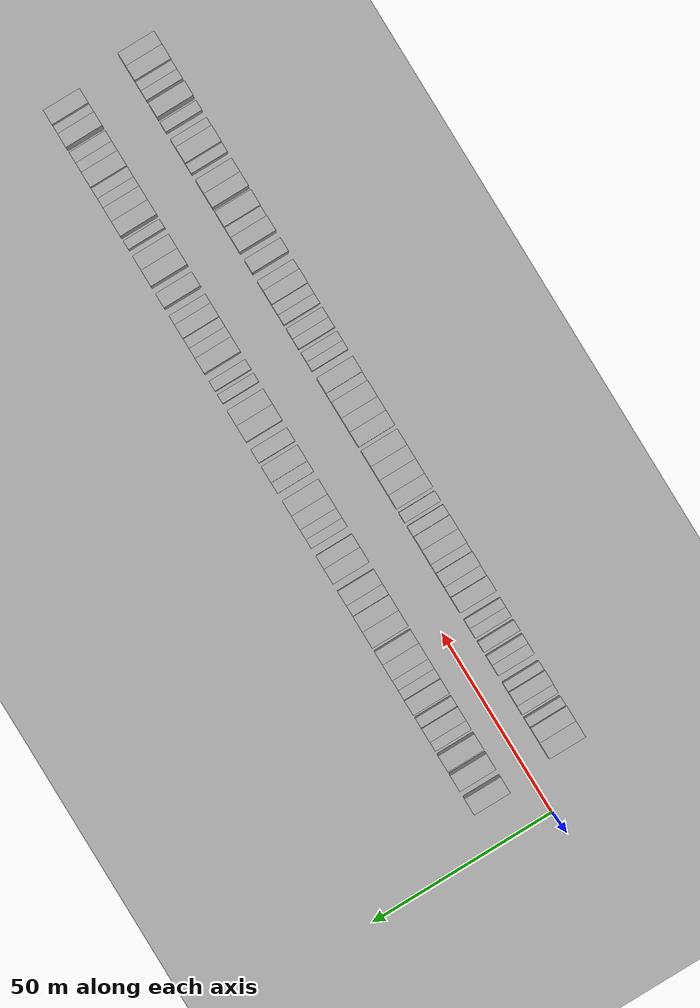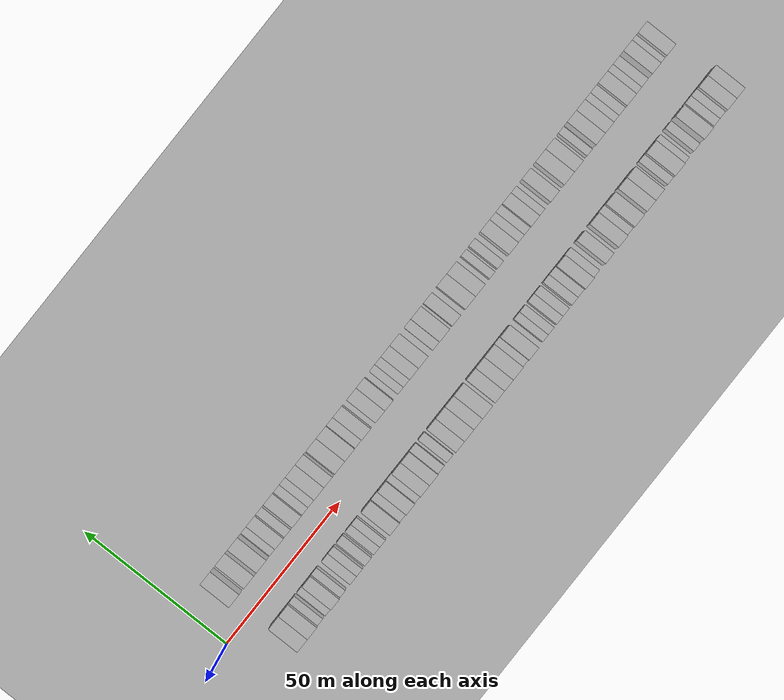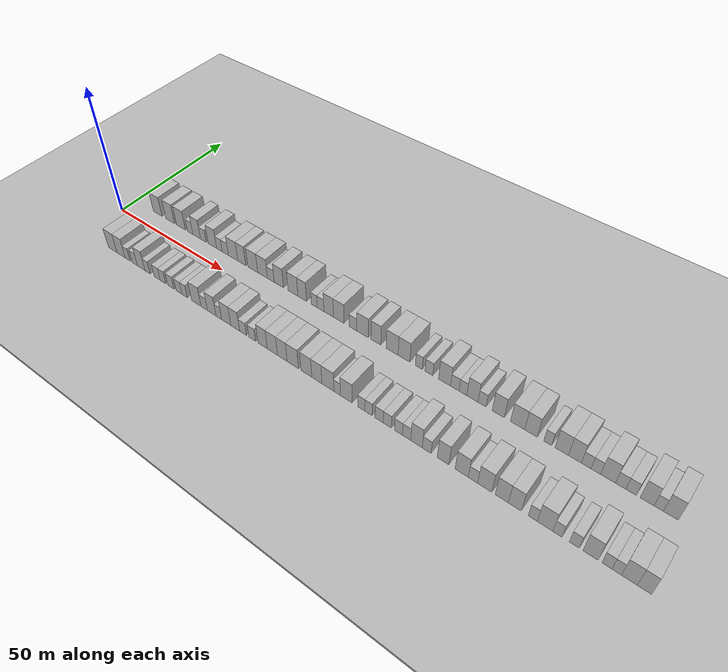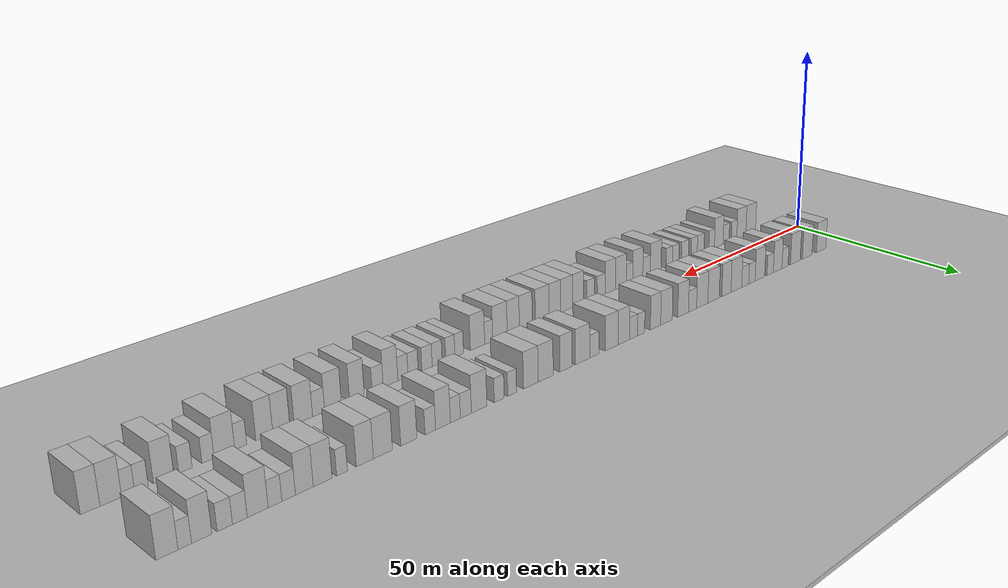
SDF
<?xml version="1.0" encoding="utf-8"?>

<sdf version="1.6">

   <world name="default">

      <gui fullscreen="0">

         <camera name="user_camera">

            <pose>-15 0 4.57585 0 0 0</pose>

            <view_controller>orbit</view_controller>

         </camera>

      </gui>

      <scene>

         <sky>

           <clouds>

             <speed>12</speed>

           </clouds>

         </sky>

         <ambient>0.4 0.4 0.4 1</ambient>

         <background>0.7 0.7 0.7 1</background>

         <shadows>1</shadows>

      </scene>

      <gravity>0 0 -9.8066</gravity>

      <magnetic_field>6e-06 2.3e-05 -4.2e-05</magnetic_field>

      <physics default="0" name="default_physics" type="ode">

         <ode>

            <solver>

               <type>quick</type>

               <iters>10</iters>

               <sor>1.0</sor>

               <use_dynamic_moi_rescaling>0</use_dynamic_moi_rescaling>

            </solver>

            <constraints>

               <cfm>0</cfm>

               <erp>0.2</erp>

               <contact_max_correcting_vel>100</contact_max_correcting_vel>

               <contact_surface_layer>0.001</contact_surface_layer>

            </constraints>

         </ode>

         <max_step_size>0.004</max_step_size>

         <real_time_factor>1</real_time_factor>

         <real_time_update_rate>250</real_time_update_rate>

      </physics>

      <light name="sun" type="directional">

         <cast_shadows>1</cast_shadows>

         <pose>0 0 10 0 0 0</pose>

         <diffuse>0.8 0.8 0.8 1</diffuse>

         <specular>0.2 0.2 0.2 1</specular>

         <attenuation>

            <range>1000</range>

            <constant>0.9</constant>

            <linear>0.01</linear>

            <quadratic>0.001</quadratic>

         </attenuation>

         <direction>-0.5 0.1 -0.9</direction>

      </light>

      <include>

         <name>ground_plane_1</name>

         <uri>model://HANNAS_ground_plane</uri>

         <pose>0 0 0  0 0 0</pose>

      </include>

      <include>

         <name>ground_plane_2</name>

         <uri>model://HANNAS_ground_plane</uri>

         <pose>100 0 0  0 0 0</pose>

      </include>

      <model name="building_1">

         <static>1</static>

         <pose frame="">12.2322 11.0000 0 0.000000 0.000000 1.570796</pose>

         <link name="link">

            <pose frame="">0 0 4.50 0 0 0</pose>

            <collision name="collision">

               <geometry>

                  <box>

                     <size>10.0000 4.4645 9.0000</size>

                  </box>

               </geometry>

               <max_contacts>10</max_contacts>

               <surface>

                  <contact>

                     <ode/>

                  </contact>

                  <bounce/>

                  <friction>

                     <torsional>

                        <ode/>

                     </torsional>

                     <ode/>

                  </friction>

               </surface>

            </collision>

            <visual name="visual">

               <cast_shadows>0</cast_shadows>

               <geometry>

                  <box>

                     <size>10.0000 4.4645 9.0000</size>

                  </box>

               </geometry>

               <material>

                  <script>

                     <uri>model://HANNAS_wall/materials/scripts</uri>

                     <uri>model://HANNAS_wall/materials/textures</uri>

                     <name>vrc/HANNAS_wall</name>

                  </script>

               </material>

            </visual>

            <self_collide>0</self_collide>

            <enable_wind>0</enable_wind>

            <kinematic>0</kinematic>

         </link>

      </model>

      <model name="building_2">

         <static>1</static>

         <pose frame="">18.6756 11.0000 0 0.000000 0.000000 1.570796</pose>

         <link name="link">

            <pose frame="">0 0 4.50 0 0 0</pose>

            <collision name="collision">

               <geometry>

                  <box>

                     <size>10.0000 4.4222 9.0000</size>

                  </box>

               </geometry>

               <max_contacts>10</max_contacts>

               <surface>

                  <contact>

                     <ode/>

                  </contact>

                  <bounce/>

                  <friction>

                     <torsional>

                        <ode/>

                     </torsional>

                     <ode/>

                  </friction>

               </surface>

            </collision>

            <visual name="visual">

               <cast_shadows>0</cast_shadows>

               <geometry>

                  <box>

                     <size>10.0000 4.4222 9.0000</size>

                  </box>

               </geometry>

               <material>

                  <script>

                     <uri>model://HANNAS_wall/materials/scripts</uri>

                     <uri>model://HANNAS_wall/materials/textures</uri>

                     <name>vrc/HANNAS_wall</name>

                  </script>

               </material>

            </visual>

            <self_collide>0</self_collide>

            <enable_wind>0</enable_wind>

            <kinematic>0</kinematic>

         </link>

      </model>

      <model name="building_3">

         <static>1</static>

         <pose frame="">24.0874 11.0000 0 0.000000 0.000000 1.570796</pose>

         <link name="link">

            <pose frame="">0 0 4.50 0 0 0</pose>

            <collision name="collision">

               <geometry>

                  <box>

                     <size>10.0000 4.4014 9.0000</size>

                  </box>

               </geometry>

               <max_contacts>10</max_contacts>

               <surface>

                  <contact>

                     <ode/>

                  </contact>

                  <bounce/>

                  <friction>

                     <torsional>

                        <ode/>

                     </torsional>

                     <ode/>

                  </friction>

               </surface>

            </collision>

            <visual name="visual">

               <cast_shadows>0</cast_shadows>

               <geometry>

                  <box>

                     <size>10.0000 4.4014 9.0000</size>

                  </box>

               </geometry>

               <material>

                  <script>

                     <uri>model://HANNAS_wall/materials/scripts</uri>

                     <uri>model://HANNAS_wall/materials/textures</uri>

                     <name>vrc/HANNAS_wall</name>

                  </script>

               </material>

            </visual>

            <self_collide>0</self_collide>

            <enable_wind>0</enable_wind>

            <kinematic>0</kinematic>

         </link>

      </model>

      <model name="building_4">

         <static>1</static>

         <pose frame="">28.6527 11.0000 0 0.000000 0.000000 1.570796</pose>

         <link name="link">

            <pose frame="">0 0 3.00 0 0 0</pose>

            <collision name="collision">

               <geometry>

                  <box>

                     <size>10.0000 2.7294 6.0000</size>

                  </box>

               </geometry>

               <max_contacts>10</max_contacts>

               <surface>

                  <contact>

                     <ode/>

                  </contact>

                  <bounce/>

                  <friction>

                     <torsional>

                        <ode/>

                     </torsional>

                     <ode/>

                  </friction>

               </surface>

            </collision>

            <visual name="visual">

               <cast_shadows>0</cast_shadows>

               <geometry>

                  <box>

                     <size>10.0000 2.7294 6.0000</size>

                  </box>

               </geometry>

               <material>

                  <script>

                     <uri>model://HANNAS_wall/materials/scripts</uri>

                     <uri>model://HANNAS_wall/materials/textures</uri>

                     <name>vrc/HANNAS_wall</name>

                  </script>

               </material>

            </visual>

            <self_collide>0</self_collide>

            <enable_wind>0</enable_wind>

            <kinematic>0</kinematic>

         </link>

      </model>

      <model name="building_5">

         <static>1</static>

         <pose frame="">31.8860 11.0000 0 0.000000 0.000000 1.570796</pose>

         <link name="link">

            <pose frame="">0 0 4.50 0 0 0</pose>

            <collision name="collision">

               <geometry>

                  <box>

                     <size>10.0000 3.7371 9.0000</size>

                  </box>

               </geometry>

               <max_contacts>10</max_contacts>

               <surface>

                  <contact>

                     <ode/>

                  </contact>

                  <bounce/>

                  <friction>

                     <torsional>

                        <ode/>

                     </torsional>

                     <ode/>

                  </friction>

               </surface>

            </collision>

            <visual name="visual">

               <cast_shadows>0</cast_shadows>

               <geometry>

                  <box>

                     <size>10.0000 3.7371 9.0000</size>

                  </box>

               </geometry>

               <material>

                  <script>

                     <uri>model://HANNAS_wall/materials/scripts</uri>

                     <uri>model://HANNAS_wall/materials/textures</uri>

                     <name>vrc/HANNAS_wall</name>

                  </script>

               </material>

            </visual>

            <self_collide>0</self_collide>

            <enable_wind>0</enable_wind>

            <kinematic>0</kinematic>

         </link>

      </model>

      <model name="building_6">

         <static>1</static>

         <pose frame="">35.1066 11.0000 0 0.000000 0.000000 1.570796</pose>

         <link name="link">

            <pose frame="">0 0 3.00 0 0 0</pose>

            <collision name="collision">

               <geometry>

                  <box>

                     <size>10.0000 2.7041 6.0000</size>

                  </box>

               </geometry>

               <max_contacts>10</max_contacts>

               <surface>

                  <contact>

                     <ode/>

                  </contact>

                  <bounce/>

                  <friction>

                     <torsional>

                        <ode/>

                     </torsional>

                     <ode/>

                  </friction>

               </surface>

            </collision>

            <visual name="visual">

               <cast_shadows>0</cast_shadows>

               <geometry>

                  <box>

                     <size>10.0000 2.7041 6.0000</size>

                  </box>

               </geometry>

               <material>

                  <script>

                     <uri>model://HANNAS_wall/materials/scripts</uri>

                     <uri>model://HANNAS_wall/materials/textures</uri>

                     <name>vrc/HANNAS_wall</name>

                  </script>

               </material>

            </visual>

            <self_collide>0</self_collide>

            <enable_wind>0</enable_wind>

            <kinematic>0</kinematic>

         </link>

      </model>

      <model name="building_7">

         <static>1</static>

         <pose frame="">39.4706 11.0000 0 0.000000 0.000000 1.570796</pose>

         <link name="link">

            <pose frame="">0 0 4.50 0 0 0</pose>

            <collision name="collision">

               <geometry>

                  <box>

                     <size>10.0000 4.0238 9.0000</size>

                  </box>

               </geometry>

               <max_contacts>10</max_contacts>

               <surface>

                  <contact>

                     <ode/>

                  </contact>

                  <bounce/>

                  <friction>

                     <torsional>

                        <ode/>

                     </torsional>

                     <ode/>

                  </friction>

               </surface>

            </collision>

            <visual name="visual">

               <cast_shadows>0</cast_shadows>

               <geometry>

                  <box>

                     <size>10.0000 4.0238 9.0000</size>

                  </box>

               </geometry>

               <material>

                  <script>

                     <uri>model://HANNAS_wall/materials/scripts</uri>

                     <uri>model://HANNAS_wall/materials/textures</uri>

                     <name>vrc/HANNAS_wall</name>

                  </script>

               </material>

            </visual>

            <self_collide>0</self_collide>

            <enable_wind>0</enable_wind>

            <kinematic>0</kinematic>

         </link>

      </model>

      <model name="building_8">

         <static>1</static>

         <pose frame="">42.8065 11.0000 0 0.000000 0.000000 1.570796</pose>

         <link name="link">

            <pose frame="">0 0 3.00 0 0 0</pose>

            <collision name="collision">

               <geometry>

                  <box>

                     <size>10.0000 2.6480 6.0000</size>

                  </box>

               </geometry>

               <max_contacts>10</max_contacts>

               <surface>

                  <contact>

                     <ode/>

                  </contact>

                  <bounce/>

                  <friction>

                     <torsional>

                        <ode/>

                     </torsional>

                     <ode/>

                  </friction>

               </surface>

            </collision>

            <visual name="visual">

               <cast_shadows>0</cast_shadows>

               <geometry>

                  <box>

                     <size>10.0000 2.6480 6.0000</size>

                  </box>

               </geometry>

               <material>

                  <script>

                     <uri>model://HANNAS_wall/materials/scripts</uri>

                     <uri>model://HANNAS_wall/materials/textures</uri>

                     <name>vrc/HANNAS_wall</name>

                  </script>

               </material>

            </visual>

            <self_collide>0</self_collide>

            <enable_wind>0</enable_wind>

            <kinematic>0</kinematic>

         </link>

      </model>

      <model name="building_9">

         <static>1</static>

         <pose frame="">45.5730 11.0000 0 0.000000 0.000000 1.570796</pose>

         <link name="link">

            <pose frame="">0 0 3.00 0 0 0</pose>

            <collision name="collision">

               <geometry>

                  <box>

                     <size>10.0000 2.8849 6.0000</size>

                  </box>

               </geometry>

               <max_contacts>10</max_contacts>

               <surface>

                  <contact>

                     <ode/>

                  </contact>

                  <bounce/>

                  <friction>

                     <torsional>

                        <ode/>

                     </torsional>

                     <ode/>

                  </friction>

               </surface>

            </collision>

            <visual name="visual">

               <cast_shadows>0</cast_shadows>

               <geometry>

                  <box>

                     <size>10.0000 2.8849 6.0000</size>

                  </box>

               </geometry>

               <material>

                  <script>

                     <uri>model://HANNAS_wall/materials/scripts</uri>

                     <uri>model://HANNAS_wall/materials/textures</uri>

                     <name>vrc/HANNAS_wall</name>

                  </script>

               </material>

            </visual>

            <self_collide>0</self_collide>

            <enable_wind>0</enable_wind>

            <kinematic>0</kinematic>

         </link>

      </model>

      <model name="building_10">

         <static>1</static>

         <pose frame="">49.1811 11.0000 0 0.000000 0.000000 1.570796</pose>

         <link name="link">

            <pose frame="">0 0 4.50 0 0 0</pose>

            <collision name="collision">

               <geometry>

                  <box>

                     <size>10.0000 4.3313 9.0000</size>

                  </box>

               </geometry>

               <max_contacts>10</max_contacts>

               <surface>

                  <contact>

                     <ode/>

                  </contact>

                  <bounce/>

                  <friction>

                     <torsional>

                        <ode/>

                     </torsional>

                     <ode/>

                  </friction>

               </surface>

            </collision>

            <visual name="visual">

               <cast_shadows>0</cast_shadows>

               <geometry>

                  <box>

                     <size>10.0000 4.3313 9.0000</size>

                  </box>

               </geometry>

               <material>

                  <script>

                     <uri>model://HANNAS_wall/materials/scripts</uri>

                     <uri>model://HANNAS_wall/materials/textures</uri>

                     <name>vrc/HANNAS_wall</name>

                  </script>

               </material>

            </visual>

            <self_collide>0</self_collide>

            <enable_wind>0</enable_wind>

            <kinematic>0</kinematic>

         </link>

      </model>

      <model name="building_11">

         <static>1</static>

         <pose frame="">53.1576 11.0000 0 0.000000 0.000000 1.570796</pose>

         <link name="link">

            <pose frame="">0 0 4.50 0 0 0</pose>

            <collision name="collision">

               <geometry>

                  <box>

                     <size>10.0000 3.6218 9.0000</size>

                  </box>

               </geometry>

               <max_contacts>10</max_contacts>

               <surface>

                  <contact>

                     <ode/>

                  </contact>

                  <bounce/>

                  <friction>

                     <torsional>

                        <ode/>

                     </torsional>

                     <ode/>

                  </friction>

               </surface>

            </collision>

            <visual name="visual">

               <cast_shadows>0</cast_shadows>

               <geometry>

                  <box>

                     <size>10.0000 3.6218 9.0000</size>

                  </box>

               </geometry>

               <material>

                  <script>

                     <uri>model://HANNAS_wall/materials/scripts</uri>

                     <uri>model://HANNAS_wall/materials/textures</uri>

                     <name>vrc/HANNAS_wall</name>

                  </script>

               </material>

            </visual>

            <self_collide>0</self_collide>

            <enable_wind>0</enable_wind>

            <kinematic>0</kinematic>

         </link>

      </model>

      <model name="building_12">

         <static>1</static>

         <pose frame="">58.1856 11.0000 0 0.000000 0.000000 1.570796</pose>

         <link name="link">

            <pose frame="">0 0 4.50 0 0 0</pose>

            <collision name="collision">

               <geometry>

                  <box>

                     <size>10.0000 4.4344 9.0000</size>

                  </box>

               </geometry>

               <max_contacts>10</max_contacts>

               <surface>

                  <contact>

                     <ode/>

                  </contact>

                  <bounce/>

                  <friction>

                     <torsional>

                        <ode/>

                     </torsional>

                     <ode/>

                  </friction>

               </surface>

            </collision>

            <visual name="visual">

               <cast_shadows>0</cast_shadows>

               <geometry>

                  <box>

                     <size>10.0000 4.4344 9.0000</size>

                  </box>

               </geometry>

               <material>

                  <script>

                     <uri>model://HANNAS_wall/materials/scripts</uri>

                     <uri>model://HANNAS_wall/materials/textures</uri>

                     <name>vrc/HANNAS_wall</name>

                  </script>

               </material>

            </visual>

            <self_collide>0</self_collide>

            <enable_wind>0</enable_wind>

            <kinematic>0</kinematic>

         </link>

      </model>

      <model name="building_13">

         <static>1</static>

         <pose frame="">62.5479 11.0000 0 0.000000 0.000000 1.570796</pose>

         <link name="link">

            <pose frame="">0 0 4.50 0 0 0</pose>

            <collision name="collision">

               <geometry>

                  <box>

                     <size>10.0000 4.2901 9.0000</size>

                  </box>

               </geometry>

               <max_contacts>10</max_contacts>

               <surface>

                  <contact>

                     <ode/>

                  </contact>

                  <bounce/>

                  <friction>

                     <torsional>

                        <ode/>

                     </torsional>

                     <ode/>

                  </friction>

               </surface>

            </collision>

            <visual name="visual">

               <cast_shadows>0</cast_shadows>

               <geometry>

                  <box>

                     <size>10.0000 4.2901 9.0000</size>

                  </box>

               </geometry>

               <material>

                  <script>

                     <uri>model://HANNAS_wall/materials/scripts</uri>

                     <uri>model://HANNAS_wall/materials/textures</uri>

                     <name>vrc/HANNAS_wall</name>

                  </script>

               </material>

            </visual>

            <self_collide>0</self_collide>

            <enable_wind>0</enable_wind>

            <kinematic>0</kinematic>

         </link>

      </model>

      <model name="building_14">

         <static>1</static>

         <pose frame="">66.1876 11.0000 0 0.000000 0.000000 1.570796</pose>

         <link name="link">

            <pose frame="">0 0 3.00 0 0 0</pose>

            <collision name="collision">

               <geometry>

                  <box>

                     <size>10.0000 2.9893 6.0000</size>

                  </box>

               </geometry>

               <max_contacts>10</max_contacts>

               <surface>

                  <contact>

                     <ode/>

                  </contact>

                  <bounce/>

                  <friction>

                     <torsional>

                        <ode/>

                     </torsional>

                     <ode/>

                  </friction>

               </surface>

            </collision>

            <visual name="visual">

               <cast_shadows>0</cast_shadows>

               <geometry>

                  <box>

                     <size>10.0000 2.9893 6.0000</size>

                  </box>

               </geometry>

               <material>

                  <script>

                     <uri>model://HANNAS_wall/materials/scripts</uri>

                     <uri>model://HANNAS_wall/materials/textures</uri>

                     <name>vrc/HANNAS_wall</name>

                  </script>

               </material>

            </visual>

            <self_collide>0</self_collide>

            <enable_wind>0</enable_wind>

            <kinematic>0</kinematic>

         </link>

      </model>

      <model name="building_15">

         <static>1</static>

         <pose frame="">69.6649 11.0000 0 0.000000 0.000000 1.570796</pose>

         <link name="link">

            <pose frame="">0 0 4.50 0 0 0</pose>

            <collision name="collision">

               <geometry>

                  <box>

                     <size>10.0000 3.9653 9.0000</size>

                  </box>

               </geometry>

               <max_contacts>10</max_contacts>

               <surface>

                  <contact>

                     <ode/>

                  </contact>

                  <bounce/>

                  <friction>

                     <torsional>

                        <ode/>

                     </torsional>

                     <ode/>

                  </friction>

               </surface>

            </collision>

            <visual name="visual">

               <cast_shadows>0</cast_shadows>

               <geometry>

                  <box>

                     <size>10.0000 3.9653 9.0000</size>

                  </box>

               </geometry>

               <material>

                  <script>

                     <uri>model://HANNAS_wall/materials/scripts</uri>

                     <uri>model://HANNAS_wall/materials/textures</uri>

                     <name>vrc/HANNAS_wall</name>

                  </script>

               </material>

            </visual>

            <self_collide>0</self_collide>

            <enable_wind>0</enable_wind>

            <kinematic>0</kinematic>

         </link>

      </model>

      <model name="building_16">

         <static>1</static>

         <pose frame="">75.7314 11.0000 0 0.000000 0.000000 1.570796</pose>

         <link name="link">

            <pose frame="">0 0 4.50 0 0 0</pose>

            <collision name="collision">

               <geometry>

                  <box>

                     <size>10.0000 4.1677 9.0000</size>

                  </box>

               </geometry>

               <max_contacts>10</max_contacts>

               <surface>

                  <contact>

                     <ode/>

                  </contact>

                  <bounce/>

                  <friction>

                     <torsional>

                        <ode/>

                     </torsional>

                     <ode/>

                  </friction>

               </surface>

            </collision>

            <visual name="visual">

               <cast_shadows>0</cast_shadows>

               <geometry>

                  <box>

                     <size>10.0000 4.1677 9.0000</size>

                  </box>

               </geometry>

               <material>

                  <script>

                     <uri>model://HANNAS_wall/materials/scripts</uri>

                     <uri>model://HANNAS_wall/materials/textures</uri>

                     <name>vrc/HANNAS_wall</name>

                  </script>

               </material>

            </visual>

            <self_collide>0</self_collide>

            <enable_wind>0</enable_wind>

            <kinematic>0</kinematic>

         </link>

      </model>

      <model name="building_17">

         <static>1</static>

         <pose frame="">79.6209 11.0000 0 0.000000 0.000000 1.570796</pose>

         <link name="link">

            <pose frame="">0 0 4.50 0 0 0</pose>

            <collision name="collision">

               <geometry>

                  <box>

                     <size>10.0000 3.6112 9.0000</size>

                  </box>

               </geometry>

               <max_contacts>10</max_contacts>

               <surface>

                  <contact>

                     <ode/>

                  </contact>

                  <bounce/>

                  <friction>

                     <torsional>

                        <ode/>

                     </torsional>

                     <ode/>

                  </friction>

               </surface>

            </collision>

            <visual name="visual">

               <cast_shadows>0</cast_shadows>

               <geometry>

                  <box>

                     <size>10.0000 3.6112 9.0000</size>

                  </box>

               </geometry>

               <material>

                  <script>

                     <uri>model://HANNAS_wall/materials/scripts</uri>

                     <uri>model://HANNAS_wall/materials/textures</uri>

                     <name>vrc/HANNAS_wall</name>

                  </script>

               </material>

            </visual>

            <self_collide>0</self_collide>

            <enable_wind>0</enable_wind>

            <kinematic>0</kinematic>

         </link>

      </model>

      <model name="building_18">

         <static>1</static>

         <pose frame="">84.6441 11.0000 0 0.000000 0.000000 1.570796</pose>

         <link name="link">

            <pose frame="">0 0 3.00 0 0 0</pose>

            <collision name="collision">

               <geometry>

                  <box>

                     <size>10.0000 2.4352 6.0000</size>

                  </box>

               </geometry>

               <max_contacts>10</max_contacts>

               <surface>

                  <contact>

                     <ode/>

                  </contact>

                  <bounce/>

                  <friction>

                     <torsional>

                        <ode/>

                     </torsional>

                     <ode/>

                  </friction>

               </surface>

            </collision>

            <visual name="visual">

               <cast_shadows>0</cast_shadows>

               <geometry>

                  <box>

                     <size>10.0000 2.4352 6.0000</size>

                  </box>

               </geometry>

               <material>

                  <script>

                     <uri>model://HANNAS_wall/materials/scripts</uri>

                     <uri>model://HANNAS_wall/materials/textures</uri>

                     <name>vrc/HANNAS_wall</name>

                  </script>

               </material>

            </visual>

            <self_collide>0</self_collide>

            <enable_wind>0</enable_wind>

            <kinematic>0</kinematic>

         </link>

      </model>

      <model name="building_19">

         <static>1</static>

         <pose frame="">87.2198 11.0000 0 0.000000 0.000000 1.570796</pose>

         <link name="link">

            <pose frame="">0 0 3.00 0 0 0</pose>

            <collision name="collision">

               <geometry>

                  <box>

                     <size>10.0000 2.7161 6.0000</size>

                  </box>

               </geometry>

               <max_contacts>10</max_contacts>

               <surface>

                  <contact>

                     <ode/>

                  </contact>

                  <bounce/>

                  <friction>

                     <torsional>

                        <ode/>

                     </torsional>

                     <ode/>

                  </friction>

               </surface>

            </collision>

            <visual name="visual">

               <cast_shadows>0</cast_shadows>

               <geometry>

                  <box>

                     <size>10.0000 2.7161 6.0000</size>

                  </box>

               </geometry>

               <material>

                  <script>

                     <uri>model://HANNAS_wall/materials/scripts</uri>

                     <uri>model://HANNAS_wall/materials/textures</uri>

                     <name>vrc/HANNAS_wall</name>

                  </script>

               </material>

            </visual>

            <self_collide>0</self_collide>

            <enable_wind>0</enable_wind>

            <kinematic>0</kinematic>

         </link>

      </model>

      <model name="building_20">

         <static>1</static>

         <pose frame="">90.5099 11.0000 0 0.000000 0.000000 1.570796</pose>

         <link name="link">

            <pose frame="">0 0 4.50 0 0 0</pose>

            <collision name="collision">

               <geometry>

                  <box>

                     <size>10.0000 3.8641 9.0000</size>

                  </box>

               </geometry>

               <max_contacts>10</max_contacts>

               <surface>

                  <contact>

                     <ode/>

                  </contact>

                  <bounce/>

                  <friction>

                     <torsional>

                        <ode/>

                     </torsional>

                     <ode/>

                  </friction>

               </surface>

            </collision>

            <visual name="visual">

               <cast_shadows>0</cast_shadows>

               <geometry>

                  <box>

                     <size>10.0000 3.8641 9.0000</size>

                  </box>

               </geometry>

               <material>

                  <script>

                     <uri>model://HANNAS_wall/materials/scripts</uri>

                     <uri>model://HANNAS_wall/materials/textures</uri>

                     <name>vrc/HANNAS_wall</name>

                  </script>

               </material>

            </visual>

            <self_collide>0</self_collide>

            <enable_wind>0</enable_wind>

            <kinematic>0</kinematic>

         </link>

      </model>

      <model name="building_21">

         <static>1</static>

         <pose frame="">94.5507 11.0000 0 0.000000 0.000000 1.570796</pose>

         <link name="link">

            <pose frame="">0 0 4.50 0 0 0</pose>

            <collision name="collision">

               <geometry>

                  <box>

                     <size>10.0000 4.2173 9.0000</size>

                  </box>

               </geometry>

               <max_contacts>10</max_contacts>

               <surface>

                  <contact>

                     <ode/>

                  </contact>

                  <bounce/>

                  <friction>

                     <torsional>

                        <ode/>

                     </torsional>

                     <ode/>

                  </friction>

               </surface>

            </collision>

            <visual name="visual">

               <cast_shadows>0</cast_shadows>

               <geometry>

                  <box>

                     <size>10.0000 4.2173 9.0000</size>

                  </box>

               </geometry>

               <material>

                  <script>

                     <uri>model://HANNAS_wall/materials/scripts</uri>

                     <uri>model://HANNAS_wall/materials/textures</uri>

                     <name>vrc/HANNAS_wall</name>

                  </script>

               </material>

            </visual>

            <self_collide>0</self_collide>

            <enable_wind>0</enable_wind>

            <kinematic>0</kinematic>

         </link>

      </model>

      <model name="building_22">

         <static>1</static>

         <pose frame="">100.1274 11.0000 0 0.000000 0.000000 1.570796</pose>

         <link name="link">

            <pose frame="">0 0 3.00 0 0 0</pose>

            <collision name="collision">

               <geometry>

                  <box>

                     <size>10.0000 2.9361 6.0000</size>

                  </box>

               </geometry>

               <max_contacts>10</max_contacts>

               <surface>

                  <contact>

                     <ode/>

                  </contact>

                  <bounce/>

                  <friction>

                     <torsional>

                        <ode/>

                     </torsional>

                     <ode/>

                  </friction>

               </surface>

            </collision>

            <visual name="visual">

               <cast_shadows>0</cast_shadows>

               <geometry>

                  <box>

                     <size>10.0000 2.9361 6.0000</size>

                  </box>

               </geometry>

               <material>

                  <script>

                     <uri>model://HANNAS_wall/materials/scripts</uri>

                     <uri>model://HANNAS_wall/materials/textures</uri>

                     <name>vrc/HANNAS_wall</name>

                  </script>

               </material>

            </visual>

            <self_collide>0</self_collide>

            <enable_wind>0</enable_wind>

            <kinematic>0</kinematic>

         </link>

      </model>

      <model name="building_23">

         <static>1</static>

         <pose frame="">103.8333 11.0000 0 0.000000 0.000000 1.570796</pose>

         <link name="link">

            <pose frame="">0 0 4.50 0 0 0</pose>

            <collision name="collision">

               <geometry>

                  <box>

                     <size>10.0000 4.4757 9.0000</size>

                  </box>

               </geometry>

               <max_contacts>10</max_contacts>

               <surface>

                  <contact>

                     <ode/>

                  </contact>

                  <bounce/>

                  <friction>

                     <torsional>

                        <ode/>

                     </torsional>

                     <ode/>

                  </friction>

               </surface>

            </collision>

            <visual name="visual">

               <cast_shadows>0</cast_shadows>

               <geometry>

                  <box>

                     <size>10.0000 4.4757 9.0000</size>

                  </box>

               </geometry>

               <material>

                  <script>

                     <uri>model://HANNAS_wall/materials/scripts</uri>

                     <uri>model://HANNAS_wall/materials/textures</uri>

                     <name>vrc/HANNAS_wall</name>

                  </script>

               </material>

            </visual>

            <self_collide>0</self_collide>

            <enable_wind>0</enable_wind>

            <kinematic>0</kinematic>

         </link>

      </model>

      <model name="building_24">

         <static>1</static>

         <pose frame="">108.9423 11.0000 0 0.000000 0.000000 1.570796</pose>

         <link name="link">

            <pose frame="">0 0 4.50 0 0 0</pose>

            <collision name="collision">

               <geometry>

                  <box>

                     <size>10.0000 3.7424 9.0000</size>

                  </box>

               </geometry>

               <max_contacts>10</max_contacts>

               <surface>

                  <contact>

                     <ode/>

                  </contact>

                  <bounce/>

                  <friction>

                     <torsional>

                        <ode/>

                     </torsional>

                     <ode/>

                  </friction>

               </surface>

            </collision>

            <visual name="visual">

               <cast_shadows>0</cast_shadows>

               <geometry>

                  <box>

                     <size>10.0000 3.7424 9.0000</size>

                  </box>

               </geometry>

               <material>

                  <script>

                     <uri>model://HANNAS_wall/materials/scripts</uri>

                     <uri>model://HANNAS_wall/materials/textures</uri>

                     <name>vrc/HANNAS_wall</name>

                  </script>

               </material>

            </visual>

            <self_collide>0</self_collide>

            <enable_wind>0</enable_wind>

            <kinematic>0</kinematic>

         </link>

      </model>

      <model name="building_25">

         <static>1</static>

         <pose frame="">115.0368 11.0000 0 0.000000 0.000000 1.570796</pose>

         <link name="link">

            <pose frame="">0 0 4.50 0 0 0</pose>

            <collision name="collision">

               <geometry>

                  <box>

                     <size>10.0000 4.4467 9.0000</size>

                  </box>

               </geometry>

               <max_contacts>10</max_contacts>

               <surface>

                  <contact>

                     <ode/>

                  </contact>

                  <bounce/>

                  <friction>

                     <torsional>

                        <ode/>

                     </torsional>

                     <ode/>

                  </friction>

               </surface>

            </collision>

            <visual name="visual">

               <cast_shadows>0</cast_shadows>

               <geometry>

                  <box>

                     <size>10.0000 4.4467 9.0000</size>

                  </box>

               </geometry>

               <material>

                  <script>

                     <uri>model://HANNAS_wall/materials/scripts</uri>

                     <uri>model://HANNAS_wall/materials/textures</uri>

                     <name>vrc/HANNAS_wall</name>

                  </script>

               </material>

            </visual>

            <self_collide>0</self_collide>

            <enable_wind>0</enable_wind>

            <kinematic>0</kinematic>

         </link>

      </model>

      <model name="building_26">

         <static>1</static>

         <pose frame="">119.3937 11.0000 0 0.000000 0.000000 1.570796</pose>

         <link name="link">

            <pose frame="">0 0 4.50 0 0 0</pose>

            <collision name="collision">

               <geometry>

                  <box>

                     <size>10.0000 4.2671 9.0000</size>

                  </box>

               </geometry>

               <max_contacts>10</max_contacts>

               <surface>

                  <contact>

                     <ode/>

                  </contact>

                  <bounce/>

                  <friction>

                     <torsional>

                        <ode/>

                     </torsional>

                     <ode/>

                  </friction>

               </surface>

            </collision>

            <visual name="visual">

               <cast_shadows>0</cast_shadows>

               <geometry>

                  <box>

                     <size>10.0000 4.2671 9.0000</size>

                  </box>

               </geometry>

               <material>

                  <script>

                     <uri>model://HANNAS_wall/materials/scripts</uri>

                     <uri>model://HANNAS_wall/materials/textures</uri>

                     <name>vrc/HANNAS_wall</name>

                  </script>

               </material>

            </visual>

            <self_collide>0</self_collide>

            <enable_wind>0</enable_wind>

            <kinematic>0</kinematic>

         </link>

      </model>

      <model name="building_27">

         <static>1</static>

         <pose frame="">124.7551 11.0000 0 0.000000 0.000000 1.570796</pose>

         <link name="link">

            <pose frame="">0 0 3.00 0 0 0</pose>

            <collision name="collision">

               <geometry>

                  <box>

                     <size>10.0000 2.4558 6.0000</size>

                  </box>

               </geometry>

               <max_contacts>10</max_contacts>

               <surface>

                  <contact>

                     <ode/>

                  </contact>

                  <bounce/>

                  <friction>

                     <torsional>

                        <ode/>

                     </torsional>

                     <ode/>

                  </friction>

               </surface>

            </collision>

            <visual name="visual">

               <cast_shadows>0</cast_shadows>

               <geometry>

                  <box>

                     <size>10.0000 2.4558 6.0000</size>

                  </box>

               </geometry>

               <material>

                  <script>

                     <uri>model://HANNAS_wall/materials/scripts</uri>

                     <uri>model://HANNAS_wall/materials/textures</uri>

                     <name>vrc/HANNAS_wall</name>

                  </script>

               </material>

            </visual>

            <self_collide>0</self_collide>

            <enable_wind>0</enable_wind>

            <kinematic>0</kinematic>

         </link>

      </model>

      <model name="building_28">

         <static>1</static>

         <pose frame="">128.3586 11.0000 0 0.000000 0.000000 1.570796</pose>

         <link name="link">

            <pose frame="">0 0 3.00 0 0 0</pose>

            <collision name="collision">

               <geometry>

                  <box>

                     <size>10.0000 2.7511 6.0000</size>

                  </box>

               </geometry>

               <max_contacts>10</max_contacts>

               <surface>

                  <contact>

                     <ode/>

                  </contact>

                  <bounce/>

                  <friction>

                     <torsional>

                        <ode/>

                     </torsional>

                     <ode/>

                  </friction>

               </surface>

            </collision>

            <visual name="visual">

               <cast_shadows>0</cast_shadows>

               <geometry>

                  <box>

                     <size>10.0000 2.7511 6.0000</size>

                  </box>

               </geometry>

               <material>

                  <script>

                     <uri>model://HANNAS_wall/materials/scripts</uri>

                     <uri>model://HANNAS_wall/materials/textures</uri>

                     <name>vrc/HANNAS_wall</name>

                  </script>

               </material>

            </visual>

            <self_collide>0</self_collide>

            <enable_wind>0</enable_wind>

            <kinematic>0</kinematic>

         </link>

      </model>

      <model name="building_29">

         <static>1</static>

         <pose frame="">133.8194 11.0000 0 0.000000 0.000000 1.570796</pose>

         <link name="link">

            <pose frame="">0 0 4.50 0 0 0</pose>

            <collision name="collision">

               <geometry>

                  <box>

                     <size>10.0000 4.1705 9.0000</size>

                  </box>

               </geometry>

               <max_contacts>10</max_contacts>

               <surface>

                  <contact>

                     <ode/>

                  </contact>

                  <bounce/>

                  <friction>

                     <torsional>

                        <ode/>

                     </torsional>

                     <ode/>

                  </friction>

               </surface>

            </collision>

            <visual name="visual">

               <cast_shadows>0</cast_shadows>

               <geometry>

                  <box>

                     <size>10.0000 4.1705 9.0000</size>

                  </box>

               </geometry>

               <material>

                  <script>

                     <uri>model://HANNAS_wall/materials/scripts</uri>

                     <uri>model://HANNAS_wall/materials/textures</uri>

                     <name>vrc/HANNAS_wall</name>

                  </script>

               </material>

            </visual>

            <self_collide>0</self_collide>

            <enable_wind>0</enable_wind>

            <kinematic>0</kinematic>

         </link>

      </model>

      <model name="building_30">

         <static>1</static>

         <pose frame="">137.3507 11.0000 0 0.000000 0.000000 1.570796</pose>

         <link name="link">

            <pose frame="">0 0 3.00 0 0 0</pose>

            <collision name="collision">

               <geometry>

                  <box>

                     <size>10.0000 2.8921 6.0000</size>

                  </box>

               </geometry>

               <max_contacts>10</max_contacts>

               <surface>

                  <contact>

                     <ode/>

                  </contact>

                  <bounce/>

                  <friction>

                     <torsional>

                        <ode/>

                     </torsional>

                     <ode/>

                  </friction>

               </surface>

            </collision>

            <visual name="visual">

               <cast_shadows>0</cast_shadows>

               <geometry>

                  <box>

                     <size>10.0000 2.8921 6.0000</size>

                  </box>

               </geometry>

               <material>

                  <script>

                     <uri>model://HANNAS_wall/materials/scripts</uri>

                     <uri>model://HANNAS_wall/materials/textures</uri>

                     <name>vrc/HANNAS_wall</name>

                  </script>

               </material>

            </visual>

            <self_collide>0</self_collide>

            <enable_wind>0</enable_wind>

            <kinematic>0</kinematic>

         </link>

      </model>

      <model name="building_31">

         <static>1</static>

         <pose frame="">140.0974 11.0000 0 0.000000 0.000000 1.570796</pose>

         <link name="link">

            <pose frame="">0 0 3.00 0 0 0</pose>

            <collision name="collision">

               <geometry>

                  <box>

                     <size>10.0000 2.6012 6.0000</size>

                  </box>

               </geometry>

               <max_contacts>10</max_contacts>

               <surface>

                  <contact>

                     <ode/>

                  </contact>

                  <bounce/>

                  <friction>

                     <torsional>

                        <ode/>

                     </torsional>

                     <ode/>

                  </friction>

               </surface>

            </collision>

            <visual name="visual">

               <cast_shadows>0</cast_shadows>

               <geometry>

                  <box>

                     <size>10.0000 2.6012 6.0000</size>

                  </box>

               </geometry>

               <material>

                  <script>

                     <uri>model://HANNAS_wall/materials/scripts</uri>

                     <uri>model://HANNAS_wall/materials/textures</uri>

                     <name>vrc/HANNAS_wall</name>

                  </script>

               </material>

            </visual>

            <self_collide>0</self_collide>

            <enable_wind>0</enable_wind>

            <kinematic>0</kinematic>

         </link>

      </model>

      <model name="building_32">

         <static>1</static>

         <pose frame="">143.2876 11.0000 0 0.000000 0.000000 1.570796</pose>

         <link name="link">

            <pose frame="">0 0 4.50 0 0 0</pose>

            <collision name="collision">

               <geometry>

                  <box>

                     <size>10.0000 3.7792 9.0000</size>

                  </box>

               </geometry>

               <max_contacts>10</max_contacts>

               <surface>

                  <contact>

                     <ode/>

                  </contact>

                  <bounce/>

                  <friction>

                     <torsional>

                        <ode/>

                     </torsional>

                     <ode/>

                  </friction>

               </surface>

            </collision>

            <visual name="visual">

               <cast_shadows>0</cast_shadows>

               <geometry>

                  <box>

                     <size>10.0000 3.7792 9.0000</size>

                  </box>

               </geometry>

               <material>

                  <script>

                     <uri>model://HANNAS_wall/materials/scripts</uri>

                     <uri>model://HANNAS_wall/materials/textures</uri>

                     <name>vrc/HANNAS_wall</name>

                  </script>

               </material>

            </visual>

            <self_collide>0</self_collide>

            <enable_wind>0</enable_wind>

            <kinematic>0</kinematic>

         </link>

      </model>

      <model name="building_33">

         <static>1</static>

         <pose frame="">146.5038 11.0000 0 0.000000 0.000000 1.570796</pose>

         <link name="link">

            <pose frame="">0 0 3.00 0 0 0</pose>

            <collision name="collision">

               <geometry>

                  <box>

                     <size>10.0000 2.6533 6.0000</size>

                  </box>

               </geometry>

               <max_contacts>10</max_contacts>

               <surface>

                  <contact>

                     <ode/>

                  </contact>

                  <bounce/>

                  <friction>

                     <torsional>

                        <ode/>

                     </torsional>

                     <ode/>

                  </friction>

               </surface>

            </collision>

            <visual name="visual">

               <cast_shadows>0</cast_shadows>

               <geometry>

                  <box>

                     <size>10.0000 2.6533 6.0000</size>

                  </box>

               </geometry>

               <material>

                  <script>

                     <uri>model://HANNAS_wall/materials/scripts</uri>

                     <uri>model://HANNAS_wall/materials/textures</uri>

                     <name>vrc/HANNAS_wall</name>

                  </script>

               </material>

            </visual>

            <self_collide>0</self_collide>

            <enable_wind>0</enable_wind>

            <kinematic>0</kinematic>

         </link>

      </model>

      <model name="building_34">

         <static>1</static>

         <pose frame="">151.7915 11.0000 0 0.000000 0.000000 1.570796</pose>

         <link name="link">

            <pose frame="">0 0 4.50 0 0 0</pose>

            <collision name="collision">

               <geometry>

                  <box>

                     <size>10.0000 3.9221 9.0000</size>

                  </box>

               </geometry>

               <max_contacts>10</max_contacts>

               <surface>

                  <contact>

                     <ode/>

                  </contact>

                  <bounce/>

                  <friction>

                     <torsional>

                        <ode/>

                     </torsional>

                     <ode/>

                  </friction>

               </surface>

            </collision>

            <visual name="visual">

               <cast_shadows>0</cast_shadows>

               <geometry>

                  <box>

                     <size>10.0000 3.9221 9.0000</size>

                  </box>

               </geometry>

               <material>

                  <script>

                     <uri>model://HANNAS_wall/materials/scripts</uri>

                     <uri>model://HANNAS_wall/materials/textures</uri>

                     <name>vrc/HANNAS_wall</name>

                  </script>

               </material>

            </visual>

            <self_collide>0</self_collide>

            <enable_wind>0</enable_wind>

            <kinematic>0</kinematic>

         </link>

      </model>

      <model name="building_35">

         <static>1</static>

         <pose frame="">157.9924 11.0000 0 0.000000 0.000000 1.570796</pose>

         <link name="link">

            <pose frame="">0 0 4.50 0 0 0</pose>

            <collision name="collision">

               <geometry>

                  <box>

                     <size>10.0000 4.4797 9.0000</size>

                  </box>

               </geometry>

               <max_contacts>10</max_contacts>

               <surface>

                  <contact>

                     <ode/>

                  </contact>

                  <bounce/>

                  <friction>

                     <torsional>

                        <ode/>

                     </torsional>

                     <ode/>

                  </friction>

               </surface>

            </collision>

            <visual name="visual">

               <cast_shadows>0</cast_shadows>

               <geometry>

                  <box>

                     <size>10.0000 4.4797 9.0000</size>

                  </box>

               </geometry>

               <material>

                  <script>

                     <uri>model://HANNAS_wall/materials/scripts</uri>

                     <uri>model://HANNAS_wall/materials/textures</uri>

                     <name>vrc/HANNAS_wall</name>

                  </script>

               </material>

            </visual>

            <self_collide>0</self_collide>

            <enable_wind>0</enable_wind>

            <kinematic>0</kinematic>

         </link>

      </model>

      <model name="building_36">

         <static>1</static>

         <pose frame="">162.1914 11.0000 0 0.000000 0.000000 1.570796</pose>

         <link name="link">

            <pose frame="">0 0 4.50 0 0 0</pose>

            <collision name="collision">

               <geometry>

                  <box>

                     <size>10.0000 3.9184 9.0000</size>

                  </box>

               </geometry>

               <max_contacts>10</max_contacts>

               <surface>

                  <contact>

                     <ode/>

                  </contact>

                  <bounce/>

                  <friction>

                     <torsional>

                        <ode/>

                     </torsional>

                     <ode/>

                  </friction>

               </surface>

            </collision>

            <visual name="visual">

               <cast_shadows>0</cast_shadows>

               <geometry>

                  <box>

                     <size>10.0000 3.9184 9.0000</size>

                  </box>

               </geometry>

               <material>

                  <script>

                     <uri>model://HANNAS_wall/materials/scripts</uri>

                     <uri>model://HANNAS_wall/materials/textures</uri>

                     <name>vrc/HANNAS_wall</name>

                  </script>

               </material>

            </visual>

            <self_collide>0</self_collide>

            <enable_wind>0</enable_wind>

            <kinematic>0</kinematic>

         </link>

      </model>

      <model name="building_37">

         <static>1</static>

         <pose frame="">167.3576 11.0000 0 0.000000 0.000000 1.570796</pose>

         <link name="link">

            <pose frame="">0 0 3.00 0 0 0</pose>

            <collision name="collision">

               <geometry>

                  <box>

                     <size>10.0000 2.4139 6.0000</size>

                  </box>

               </geometry>

               <max_contacts>10</max_contacts>

               <surface>

                  <contact>

                     <ode/>

                  </contact>

                  <bounce/>

                  <friction>

                     <torsional>

                        <ode/>

                     </torsional>

                     <ode/>

                  </friction>

               </surface>

            </collision>

            <visual name="visual">

               <cast_shadows>0</cast_shadows>

               <geometry>

                  <box>

                     <size>10.0000 2.4139 6.0000</size>

                  </box>

               </geometry>

               <material>

                  <script>

                     <uri>model://HANNAS_wall/materials/scripts</uri>

                     <uri>model://HANNAS_wall/materials/textures</uri>

                     <name>vrc/HANNAS_wall</name>

                  </script>

               </material>

            </visual>

            <self_collide>0</self_collide>

            <enable_wind>0</enable_wind>

            <kinematic>0</kinematic>

         </link>

      </model>

      <model name="building_38">

         <static>1</static>

         <pose frame="">171.5949 11.0000 0 0.000000 0.000000 1.570796</pose>

         <link name="link">

            <pose frame="">0 0 4.50 0 0 0</pose>

            <collision name="collision">

               <geometry>

                  <box>

                     <size>10.0000 4.0607 9.0000</size>

                  </box>

               </geometry>

               <max_contacts>10</max_contacts>

               <surface>

                  <contact>

                     <ode/>

                  </contact>

                  <bounce/>

                  <friction>

                     <torsional>

                        <ode/>

                     </torsional>

                     <ode/>

                  </friction>

               </surface>

            </collision>

            <visual name="visual">

               <cast_shadows>0</cast_shadows>

               <geometry>

                  <box>

                     <size>10.0000 4.0607 9.0000</size>

                  </box>

               </geometry>

               <material>

                  <script>

                     <uri>model://HANNAS_wall/materials/scripts</uri>

                     <uri>model://HANNAS_wall/materials/textures</uri>

                     <name>vrc/HANNAS_wall</name>

                  </script>

               </material>

            </visual>

            <self_collide>0</self_collide>

            <enable_wind>0</enable_wind>

            <kinematic>0</kinematic>

         </link>

      </model>

      <model name="building_39">

         <static>1</static>

         <pose frame="">175.5178 11.0000 0 0.000000 0.000000 1.570796</pose>

         <link name="link">

            <pose frame="">0 0 4.50 0 0 0</pose>

            <collision name="collision">

               <geometry>

                  <box>

                     <size>10.0000 3.7851 9.0000</size>

                  </box>

               </geometry>

               <max_contacts>10</max_contacts>

               <surface>

                  <contact>

                     <ode/>

                  </contact>

                  <bounce/>

                  <friction>

                     <torsional>

                        <ode/>

                     </torsional>

                     <ode/>

                  </friction>

               </surface>

            </collision>

            <visual name="visual">

               <cast_shadows>0</cast_shadows>

               <geometry>

                  <box>

                     <size>10.0000 3.7851 9.0000</size>

                  </box>

               </geometry>

               <material>

                  <script>

                     <uri>model://HANNAS_wall/materials/scripts</uri>

                     <uri>model://HANNAS_wall/materials/textures</uri>

                     <name>vrc/HANNAS_wall</name>

                  </script>

               </material>

            </visual>

            <self_collide>0</self_collide>

            <enable_wind>0</enable_wind>

            <kinematic>0</kinematic>

         </link>

      </model>

      <model name="building_40">

         <static>1</static>

         <pose frame="">178.8198 11.0000 0 0.000000 0.000000 1.570796</pose>

         <link name="link">

            <pose frame="">0 0 3.00 0 0 0</pose>

            <collision name="collision">

               <geometry>

                  <box>

                     <size>10.0000 2.8188 6.0000</size>

                  </box>

               </geometry>

               <max_contacts>10</max_contacts>

               <surface>

                  <contact>

                     <ode/>

                  </contact>

                  <bounce/>

                  <friction>

                     <torsional>

                        <ode/>

                     </torsional>

                     <ode/>

                  </friction>

               </surface>

            </collision>

            <visual name="visual">

               <cast_shadows>0</cast_shadows>

               <geometry>

                  <box>

                     <size>10.0000 2.8188 6.0000</size>

                  </box>

               </geometry>

               <material>

                  <script>

                     <uri>model://HANNAS_wall/materials/scripts</uri>

                     <uri>model://HANNAS_wall/materials/textures</uri>

                     <name>vrc/HANNAS_wall</name>

                  </script>

               </material>

            </visual>

            <self_collide>0</self_collide>

            <enable_wind>0</enable_wind>

            <kinematic>0</kinematic>

         </link>

      </model>

      <model name="building_41">

         <static>1</static>

         <pose frame="">181.6317 11.0000 0 0.000000 0.000000 1.570796</pose>

         <link name="link">

            <pose frame="">0 0 3.00 0 0 0</pose>

            <collision name="collision">

               <geometry>

                  <box>

                     <size>10.0000 2.8050 6.0000</size>

                  </box>

               </geometry>

               <max_contacts>10</max_contacts>

               <surface>

                  <contact>

                     <ode/>

                  </contact>

                  <bounce/>

                  <friction>

                     <torsional>

                        <ode/>

                     </torsional>

                     <ode/>

                  </friction>

               </surface>

            </collision>

            <visual name="visual">

               <cast_shadows>0</cast_shadows>

               <geometry>

                  <box>

                     <size>10.0000 2.8050 6.0000</size>

                  </box>

               </geometry>

               <material>

                  <script>

                     <uri>model://HANNAS_wall/materials/scripts</uri>

                     <uri>model://HANNAS_wall/materials/textures</uri>

                     <name>vrc/HANNAS_wall</name>

                  </script>

               </material>

            </visual>

            <self_collide>0</self_collide>

            <enable_wind>0</enable_wind>

            <kinematic>0</kinematic>

         </link>

      </model>

      <model name="building_42">

         <static>1</static>

         <pose frame="">185.1262 11.0000 0 0.000000 0.000000 1.570796</pose>

         <link name="link">

            <pose frame="">0 0 4.50 0 0 0</pose>

            <collision name="collision">

               <geometry>

                  <box>

                     <size>10.0000 4.1840 9.0000</size>

                  </box>

               </geometry>

               <max_contacts>10</max_contacts>

               <surface>

                  <contact>

                     <ode/>

                  </contact>

                  <bounce/>

                  <friction>

                     <torsional>

                        <ode/>

                     </torsional>

                     <ode/>

                  </friction>

               </surface>

            </collision>

            <visual name="visual">

               <cast_shadows>0</cast_shadows>

               <geometry>

                  <box>

                     <size>10.0000 4.1840 9.0000</size>

                  </box>

               </geometry>

               <material>

                  <script>

                     <uri>model://HANNAS_wall/materials/scripts</uri>

                     <uri>model://HANNAS_wall/materials/textures</uri>

                     <name>vrc/HANNAS_wall</name>

                  </script>

               </material>

            </visual>

            <self_collide>0</self_collide>

            <enable_wind>0</enable_wind>

            <kinematic>0</kinematic>

         </link>

      </model>

      <model name="building_43">

         <static>1</static>

         <pose frame="">188.6675 11.0000 0 0.000000 0.000000 1.570796</pose>

         <link name="link">

            <pose frame="">0 0 3.00 0 0 0</pose>

            <collision name="collision">

               <geometry>

                  <box>

                     <size>10.0000 2.8985 6.0000</size>

                  </box>

               </geometry>

               <max_contacts>10</max_contacts>

               <surface>

                  <contact>

                     <ode/>

                  </contact>

                  <bounce/>

                  <friction>

                     <torsional>

                        <ode/>

                     </torsional>

                     <ode/>

                  </friction>

               </surface>

            </collision>

            <visual name="visual">

               <cast_shadows>0</cast_shadows>

               <geometry>

                  <box>

                     <size>10.0000 2.8985 6.0000</size>

                  </box>

               </geometry>

               <material>

                  <script>

                     <uri>model://HANNAS_wall/materials/scripts</uri>

                     <uri>model://HANNAS_wall/materials/textures</uri>

                     <name>vrc/HANNAS_wall</name>

                  </script>

               </material>

            </visual>

            <self_collide>0</self_collide>

            <enable_wind>0</enable_wind>

            <kinematic>0</kinematic>

         </link>

      </model>

      <model name="building_44">

         <static>1</static>

         <pose frame="">191.5837 11.0000 0 0.000000 0.000000 1.570796</pose>

         <link name="link">

            <pose frame="">0 0 3.00 0 0 0</pose>

            <collision name="collision">

               <geometry>

                  <box>

                     <size>10.0000 2.9341 6.0000</size>

                  </box>

               </geometry>

               <max_contacts>10</max_contacts>

               <surface>

                  <contact>

                     <ode/>

                  </contact>

                  <bounce/>

                  <friction>

                     <torsional>

                        <ode/>

                     </torsional>

                     <ode/>

                  </friction>

               </surface>

            </collision>

            <visual name="visual">

               <cast_shadows>0</cast_shadows>

               <geometry>

                  <box>

                     <size>10.0000 2.9341 6.0000</size>

                  </box>

               </geometry>

               <material>

                  <script>

                     <uri>model://HANNAS_wall/materials/scripts</uri>

                     <uri>model://HANNAS_wall/materials/textures</uri>

                     <name>vrc/HANNAS_wall</name>

                  </script>

               </material>

            </visual>

            <self_collide>0</self_collide>

            <enable_wind>0</enable_wind>

            <kinematic>0</kinematic>

         </link>

      </model>

      <model name="building_45">

         <static>1</static>

         <pose frame="">195.9480 11.0000 0 0.000000 0.000000 1.570796</pose>

         <link name="link">

            <pose frame="">0 0 4.50 0 0 0</pose>

            <collision name="collision">

               <geometry>

                  <box>

                     <size>10.0000 3.7945 9.0000</size>

                  </box>

               </geometry>

               <max_contacts>10</max_contacts>

               <surface>

                  <contact>

                     <ode/>

                  </contact>

                  <bounce/>

                  <friction>

                     <torsional>

                        <ode/>

                     </torsional>

                     <ode/>

                  </friction>

               </surface>

            </collision>

            <visual name="visual">

               <cast_shadows>0</cast_shadows>

               <geometry>

                  <box>

                     <size>10.0000 3.7945 9.0000</size>

                  </box>

               </geometry>

               <material>

                  <script>

                     <uri>model://HANNAS_wall/materials/scripts</uri>

                     <uri>model://HANNAS_wall/materials/textures</uri>

                     <name>vrc/HANNAS_wall</name>

                  </script>

               </material>

            </visual>

            <self_collide>0</self_collide>

            <enable_wind>0</enable_wind>

            <kinematic>0</kinematic>

         </link>

      </model>

      <model name="building_46">

         <static>1</static>

         <pose frame="">199.0831 11.0000 0 0.000000 0.000000 1.570796</pose>

         <link name="link">

            <pose frame="">0 0 3.00 0 0 0</pose>

            <collision name="collision">

               <geometry>

                  <box>

                     <size>10.0000 2.4755 6.0000</size>

                  </box>

               </geometry>

               <max_contacts>10</max_contacts>

               <surface>

                  <contact>

                     <ode/>

                  </contact>

                  <bounce/>

                  <friction>

                     <torsional>

                        <ode/>

                     </torsional>

                     <ode/>

                  </friction>

               </surface>

            </collision>

            <visual name="visual">

               <cast_shadows>0</cast_shadows>

               <geometry>

                  <box>

                     <size>10.0000 2.4755 6.0000</size>

                  </box>

               </geometry>

               <material>

                  <script>

                     <uri>model://HANNAS_wall/materials/scripts</uri>

                     <uri>model://HANNAS_wall/materials/textures</uri>

                     <name>vrc/HANNAS_wall</name>

                  </script>

               </material>

            </visual>

            <self_collide>0</self_collide>

            <enable_wind>0</enable_wind>

            <kinematic>0</kinematic>

         </link>

      </model>

      <model name="building_47">

         <static>1</static>

         <pose frame="">202.3173 11.0000 0 0.000000 0.000000 1.570796</pose>

         <link name="link">

            <pose frame="">0 0 4.50 0 0 0</pose>

            <collision name="collision">

               <geometry>

                  <box>

                     <size>10.0000 3.9930 9.0000</size>

                  </box>

               </geometry>

               <max_contacts>10</max_contacts>

               <surface>

                  <contact>

                     <ode/>

                  </contact>

                  <bounce/>

                  <friction>

                     <torsional>

                        <ode/>

                     </torsional>

                     <ode/>

                  </friction>

               </surface>

            </collision>

            <visual name="visual">

               <cast_shadows>0</cast_shadows>

               <geometry>

                  <box>

                     <size>10.0000 3.9930 9.0000</size>

                  </box>

               </geometry>

               <material>

                  <script>

                     <uri>model://HANNAS_wall/materials/scripts</uri>

                     <uri>model://HANNAS_wall/materials/textures</uri>

                     <name>vrc/HANNAS_wall</name>

                  </script>

               </material>

            </visual>

            <self_collide>0</self_collide>

            <enable_wind>0</enable_wind>

            <kinematic>0</kinematic>

         </link>

      </model>

      <model name="building_48">

         <static>1</static>

         <pose frame="">14.2133 -11.0000 0 0.000000 0.000000 1.570796</pose>

         <link name="link">

            <pose frame="">0 0 4.50 0 0 0</pose>

            <collision name="collision">

               <geometry>

                  <box>

                     <size>10.0000 4.4266 9.0000</size>

                  </box>

               </geometry>

               <max_contacts>10</max_contacts>

               <surface>

                  <contact>

                     <ode/>

                  </contact>

                  <bounce/>

                  <friction>

                     <torsional>

                        <ode/>

                     </torsional>

                     <ode/>

                  </friction>

               </surface>

            </collision>

            <visual name="visual">

               <cast_shadows>0</cast_shadows>

               <geometry>

                  <box>

                     <size>10.0000 4.4266 9.0000</size>

                  </box>

               </geometry>

               <material>

                  <script>

                     <uri>model://HANNAS_wall/materials/scripts</uri>

                     <uri>model://HANNAS_wall/materials/textures</uri>

                     <name>vrc/HANNAS_wall</name>

                  </script>

               </material>

            </visual>

            <self_collide>0</self_collide>

            <enable_wind>0</enable_wind>

            <kinematic>0</kinematic>

         </link>

      </model>

      <model name="building_49">

         <static>1</static>

         <pose frame="">18.4835 -11.0000 0 0.000000 0.000000 1.570796</pose>

         <link name="link">

            <pose frame="">0 0 4.50 0 0 0</pose>

            <collision name="collision">

               <geometry>

                  <box>

                     <size>10.0000 4.1138 9.0000</size>

                  </box>

               </geometry>

               <max_contacts>10</max_contacts>

               <surface>

                  <contact>

                     <ode/>

                  </contact>

                  <bounce/>

                  <friction>

                     <torsional>

                        <ode/>

                     </torsional>

                     <ode/>

                  </friction>

               </surface>

            </collision>

            <visual name="visual">

               <cast_shadows>0</cast_shadows>

               <geometry>

                  <box>

                     <size>10.0000 4.1138 9.0000</size>

                  </box>

               </geometry>

               <material>

                  <script>

                     <uri>model://HANNAS_wall/materials/scripts</uri>

                     <uri>model://HANNAS_wall/materials/textures</uri>

                     <name>vrc/HANNAS_wall</name>

                  </script>

               </material>

            </visual>

            <self_collide>0</self_collide>

            <enable_wind>0</enable_wind>

            <kinematic>0</kinematic>

         </link>

      </model>

      <model name="building_50">

         <static>1</static>

         <pose frame="">21.7506 -11.0000 0 0.000000 0.000000 1.570796</pose>

         <link name="link">

            <pose frame="">0 0 3.00 0 0 0</pose>

            <collision name="collision">

               <geometry>

                  <box>

                     <size>10.0000 2.4204 6.0000</size>

                  </box>

               </geometry>

               <max_contacts>10</max_contacts>

               <surface>

                  <contact>

                     <ode/>

                  </contact>

                  <bounce/>

                  <friction>

                     <torsional>

                        <ode/>

                     </torsional>

                     <ode/>

                  </friction>

               </surface>

            </collision>

            <visual name="visual">

               <cast_shadows>0</cast_shadows>

               <geometry>

                  <box>

                     <size>10.0000 2.4204 6.0000</size>

                  </box>

               </geometry>

               <material>

                  <script>

                     <uri>model://HANNAS_wall/materials/scripts</uri>

                     <uri>model://HANNAS_wall/materials/textures</uri>

                     <name>vrc/HANNAS_wall</name>

                  </script>

               </material>

            </visual>

            <self_collide>0</self_collide>

            <enable_wind>0</enable_wind>

            <kinematic>0</kinematic>

         </link>

      </model>

      <model name="building_51">

         <static>1</static>

         <pose frame="">25.2767 -11.0000 0 0.000000 0.000000 1.570796</pose>

         <link name="link">

            <pose frame="">0 0 3.00 0 0 0</pose>

            <collision name="collision">

               <geometry>

                  <box>

                     <size>10.0000 2.6317 6.0000</size>

                  </box>

               </geometry>

               <max_contacts>10</max_contacts>

               <surface>

                  <contact>

                     <ode/>

                  </contact>

                  <bounce/>

                  <friction>

                     <torsional>

                        <ode/>

                     </torsional>

                     <ode/>

                  </friction>

               </surface>

            </collision>

            <visual name="visual">

               <cast_shadows>0</cast_shadows>

               <geometry>

                  <box>

                     <size>10.0000 2.6317 6.0000</size>

                  </box>

               </geometry>

               <material>

                  <script>

                     <uri>model://HANNAS_wall/materials/scripts</uri>

                     <uri>model://HANNAS_wall/materials/textures</uri>

                     <name>vrc/HANNAS_wall</name>

                  </script>

               </material>

            </visual>

            <self_collide>0</self_collide>

            <enable_wind>0</enable_wind>

            <kinematic>0</kinematic>

         </link>

      </model>

      <model name="building_52">

         <static>1</static>

         <pose frame="">28.4635 -11.0000 0 0.000000 0.000000 1.570796</pose>

         <link name="link">

            <pose frame="">0 0 4.50 0 0 0</pose>

            <collision name="collision">

               <geometry>

                  <box>

                     <size>10.0000 3.7420 9.0000</size>

                  </box>

               </geometry>

               <max_contacts>10</max_contacts>

               <surface>

                  <contact>

                     <ode/>

                  </contact>

                  <bounce/>

                  <friction>

                     <torsional>

                        <ode/>

                     </torsional>

                     <ode/>

                  </friction>

               </surface>

            </collision>

            <visual name="visual">

               <cast_shadows>0</cast_shadows>

               <geometry>

                  <box>

                     <size>10.0000 3.7420 9.0000</size>

                  </box>

               </geometry>

               <material>

                  <script>

                     <uri>model://HANNAS_wall/materials/scripts</uri>

                     <uri>model://HANNAS_wall/materials/textures</uri>

                     <name>vrc/HANNAS_wall</name>

                  </script>

               </material>

            </visual>

            <self_collide>0</self_collide>

            <enable_wind>0</enable_wind>

            <kinematic>0</kinematic>

         </link>

      </model>

      <model name="building_53">

         <static>1</static>

         <pose frame="">31.5537 -11.0000 0 0.000000 0.000000 1.570796</pose>

         <link name="link">

            <pose frame="">0 0 3.00 0 0 0</pose>

            <collision name="collision">

               <geometry>

                  <box>

                     <size>10.0000 2.4384 6.0000</size>

                  </box>

               </geometry>

               <max_contacts>10</max_contacts>

               <surface>

                  <contact>

                     <ode/>

                  </contact>

                  <bounce/>

                  <friction>

                     <torsional>

                        <ode/>

                     </torsional>

                     <ode/>

                  </friction>

               </surface>

            </collision>

            <visual name="visual">

               <cast_shadows>0</cast_shadows>

               <geometry>

                  <box>

                     <size>10.0000 2.4384 6.0000</size>

                  </box>

               </geometry>

               <material>

                  <script>

                     <uri>model://HANNAS_wall/materials/scripts</uri>

                     <uri>model://HANNAS_wall/materials/textures</uri>

                     <name>vrc/HANNAS_wall</name>

                  </script>

               </material>

            </visual>

            <self_collide>0</self_collide>

            <enable_wind>0</enable_wind>

            <kinematic>0</kinematic>

         </link>

      </model>

      <model name="building_54">

         <static>1</static>

         <pose frame="">36.2151 -11.0000 0 0.000000 0.000000 1.570796</pose>

         <link name="link">

            <pose frame="">0 0 3.00 0 0 0</pose>

            <collision name="collision">

               <geometry>

                  <box>

                     <size>10.0000 2.8843 6.0000</size>

                  </box>

               </geometry>

               <max_contacts>10</max_contacts>

               <surface>

                  <contact>

                     <ode/>

                  </contact>

                  <bounce/>

                  <friction>

                     <torsional>

                        <ode/>

                     </torsional>

                     <ode/>

                  </friction>

               </surface>

            </collision>

            <visual name="visual">

               <cast_shadows>0</cast_shadows>

               <geometry>

                  <box>

                     <size>10.0000 2.8843 6.0000</size>

                  </box>

               </geometry>

               <material>

                  <script>

                     <uri>model://HANNAS_wall/materials/scripts</uri>

                     <uri>model://HANNAS_wall/materials/textures</uri>

                     <name>vrc/HANNAS_wall</name>

                  </script>

               </material>

            </visual>

            <self_collide>0</self_collide>

            <enable_wind>0</enable_wind>

            <kinematic>0</kinematic>

         </link>

      </model>

      <model name="building_55">

         <static>1</static>

         <pose frame="">38.9519 -11.0000 0 0.000000 0.000000 1.570796</pose>

         <link name="link">

            <pose frame="">0 0 3.00 0 0 0</pose>

            <collision name="collision">

               <geometry>

                  <box>

                     <size>10.0000 2.5895 6.0000</size>

                  </box>

               </geometry>

               <max_contacts>10</max_contacts>

               <surface>

                  <contact>

                     <ode/>

                  </contact>

                  <bounce/>

                  <friction>

                     <torsional>

                        <ode/>

                     </torsional>

                     <ode/>

                  </friction>

               </surface>

            </collision>

            <visual name="visual">

               <cast_shadows>0</cast_shadows>

               <geometry>

                  <box>

                     <size>10.0000 2.5895 6.0000</size>

                  </box>

               </geometry>

               <material>

                  <script>

                     <uri>model://HANNAS_wall/materials/scripts</uri>

                     <uri>model://HANNAS_wall/materials/textures</uri>

                     <name>vrc/HANNAS_wall</name>

                  </script>

               </material>

            </visual>

            <self_collide>0</self_collide>

            <enable_wind>0</enable_wind>

            <kinematic>0</kinematic>

         </link>

      </model>

      <model name="building_56">

         <static>1</static>

         <pose frame="">42.6931 -11.0000 0 0.000000 0.000000 1.570796</pose>

         <link name="link">

            <pose frame="">0 0 3.00 0 0 0</pose>

            <collision name="collision">

               <geometry>

                  <box>

                     <size>10.0000 2.8928 6.0000</size>

                  </box>

               </geometry>

               <max_contacts>10</max_contacts>

               <surface>

                  <contact>

                     <ode/>

                  </contact>

                  <bounce/>

                  <friction>

                     <torsional>

                        <ode/>

                     </torsional>

                     <ode/>

                  </friction>

               </surface>

            </collision>

            <visual name="visual">

               <cast_shadows>0</cast_shadows>

               <geometry>

                  <box>

                     <size>10.0000 2.8928 6.0000</size>

                  </box>

               </geometry>

               <material>

                  <script>

                     <uri>model://HANNAS_wall/materials/scripts</uri>

                     <uri>model://HANNAS_wall/materials/textures</uri>

                     <name>vrc/HANNAS_wall</name>

                  </script>

               </material>

            </visual>

            <self_collide>0</self_collide>

            <enable_wind>0</enable_wind>

            <kinematic>0</kinematic>

         </link>

      </model>

      <model name="building_57">

         <static>1</static>

         <pose frame="">46.4579 -11.0000 0 0.000000 0.000000 1.570796</pose>

         <link name="link">

            <pose frame="">0 0 3.00 0 0 0</pose>

            <collision name="collision">

               <geometry>

                  <box>

                     <size>10.0000 2.6368 6.0000</size>

                  </box>

               </geometry>

               <max_contacts>10</max_contacts>

               <surface>

                  <contact>

                     <ode/>

                  </contact>

                  <bounce/>

                  <friction>

                     <torsional>

                        <ode/>

                     </torsional>

                     <ode/>

                  </friction>

               </surface>

            </collision>

            <visual name="visual">

               <cast_shadows>0</cast_shadows>

               <geometry>

                  <box>

                     <size>10.0000 2.6368 6.0000</size>

                  </box>

               </geometry>

               <material>

                  <script>

                     <uri>model://HANNAS_wall/materials/scripts</uri>

                     <uri>model://HANNAS_wall/materials/textures</uri>

                     <name>vrc/HANNAS_wall</name>

                  </script>

               </material>

            </visual>

            <self_collide>0</self_collide>

            <enable_wind>0</enable_wind>

            <kinematic>0</kinematic>

         </link>

      </model>

      <model name="building_58">

         <static>1</static>

         <pose frame="">49.0206 -11.0000 0 0.000000 0.000000 1.570796</pose>

         <link name="link">

            <pose frame="">0 0 3.00 0 0 0</pose>

            <collision name="collision">

               <geometry>

                  <box>

                     <size>10.0000 2.4887 6.0000</size>

                  </box>

               </geometry>

               <max_contacts>10</max_contacts>

               <surface>

                  <contact>

                     <ode/>

                  </contact>

                  <bounce/>

                  <friction>

                     <torsional>

                        <ode/>

                     </torsional>

                     <ode/>

                  </friction>

               </surface>

            </collision>

            <visual name="visual">

               <cast_shadows>0</cast_shadows>

               <geometry>

                  <box>

                     <size>10.0000 2.4887 6.0000</size>

                  </box>

               </geometry>

               <material>

                  <script>

                     <uri>model://HANNAS_wall/materials/scripts</uri>

                     <uri>model://HANNAS_wall/materials/textures</uri>

                     <name>vrc/HANNAS_wall</name>

                  </script>

               </material>

            </visual>

            <self_collide>0</self_collide>

            <enable_wind>0</enable_wind>

            <kinematic>0</kinematic>

         </link>

      </model>

      <model name="building_59">

         <static>1</static>

         <pose frame="">54.3714 -11.0000 0 0.000000 0.000000 1.570796</pose>

         <link name="link">

            <pose frame="">0 0 4.50 0 0 0</pose>

            <collision name="collision">

               <geometry>

                  <box>

                     <size>10.0000 4.2129 9.0000</size>

                  </box>

               </geometry>

               <max_contacts>10</max_contacts>

               <surface>

                  <contact>

                     <ode/>

                  </contact>

                  <bounce/>

                  <friction>

                     <torsional>

                        <ode/>

                     </torsional>

                     <ode/>

                  </friction>

               </surface>

            </collision>

            <visual name="visual">

               <cast_shadows>0</cast_shadows>

               <geometry>

                  <box>

                     <size>10.0000 4.2129 9.0000</size>

                  </box>

               </geometry>

               <material>

                  <script>

                     <uri>model://HANNAS_wall/materials/scripts</uri>

                     <uri>model://HANNAS_wall/materials/textures</uri>

                     <name>vrc/HANNAS_wall</name>

                  </script>

               </material>

            </visual>

            <self_collide>0</self_collide>

            <enable_wind>0</enable_wind>

            <kinematic>0</kinematic>

         </link>

      </model>

      <model name="building_60">

         <static>1</static>

         <pose frame="">57.9203 -11.0000 0 0.000000 0.000000 1.570796</pose>

         <link name="link">

            <pose frame="">0 0 3.00 0 0 0</pose>

            <collision name="collision">

               <geometry>

                  <box>

                     <size>10.0000 2.8849 6.0000</size>

                  </box>

               </geometry>

               <max_contacts>10</max_contacts>

               <surface>

                  <contact>

                     <ode/>

                  </contact>

                  <bounce/>

                  <friction>

                     <torsional>

                        <ode/>

                     </torsional>

                     <ode/>

                  </friction>

               </surface>

            </collision>

            <visual name="visual">

               <cast_shadows>0</cast_shadows>

               <geometry>

                  <box>

                     <size>10.0000 2.8849 6.0000</size>

                  </box>

               </geometry>

               <material>

                  <script>

                     <uri>model://HANNAS_wall/materials/scripts</uri>

                     <uri>model://HANNAS_wall/materials/textures</uri>

                     <name>vrc/HANNAS_wall</name>

                  </script>

               </material>

            </visual>

            <self_collide>0</self_collide>

            <enable_wind>0</enable_wind>

            <kinematic>0</kinematic>

         </link>

      </model>

      <model name="building_61">

         <static>1</static>

         <pose frame="">61.2550 -11.0000 0 0.000000 0.000000 1.570796</pose>

         <link name="link">

            <pose frame="">0 0 4.50 0 0 0</pose>

            <collision name="collision">

               <geometry>

                  <box>

                     <size>10.0000 3.7845 9.0000</size>

                  </box>

               </geometry>

               <max_contacts>10</max_contacts>

               <surface>

                  <contact>

                     <ode/>

                  </contact>

                  <bounce/>

                  <friction>

                     <torsional>

                        <ode/>

                     </torsional>

                     <ode/>

                  </friction>

               </surface>

            </collision>

            <visual name="visual">

               <cast_shadows>0</cast_shadows>

               <geometry>

                  <box>

                     <size>10.0000 3.7845 9.0000</size>

                  </box>

               </geometry>

               <material>

                  <script>

                     <uri>model://HANNAS_wall/materials/scripts</uri>

                     <uri>model://HANNAS_wall/materials/textures</uri>

                     <name>vrc/HANNAS_wall</name>

                  </script>

               </material>

            </visual>

            <self_collide>0</self_collide>

            <enable_wind>0</enable_wind>

            <kinematic>0</kinematic>

         </link>

      </model>

      <model name="building_62">

         <static>1</static>

         <pose frame="">64.3572 -11.0000 0 0.000000 0.000000 1.570796</pose>

         <link name="link">

            <pose frame="">0 0 3.00 0 0 0</pose>

            <collision name="collision">

               <geometry>

                  <box>

                     <size>10.0000 2.4199 6.0000</size>

                  </box>

               </geometry>

               <max_contacts>10</max_contacts>

               <surface>

                  <contact>

                     <ode/>

                  </contact>

                  <bounce/>

                  <friction>

                     <torsional>

                        <ode/>

                     </torsional>

                     <ode/>

                  </friction>

               </surface>

            </collision>

            <visual name="visual">

               <cast_shadows>0</cast_shadows>

               <geometry>

                  <box>

                     <size>10.0000 2.4199 6.0000</size>

                  </box>

               </geometry>

               <material>

                  <script>

                     <uri>model://HANNAS_wall/materials/scripts</uri>

                     <uri>model://HANNAS_wall/materials/textures</uri>

                     <name>vrc/HANNAS_wall</name>

                  </script>

               </material>

            </visual>

            <self_collide>0</self_collide>

            <enable_wind>0</enable_wind>

            <kinematic>0</kinematic>

         </link>

      </model>

      <model name="building_63">

         <static>1</static>

         <pose frame="">67.5437 -11.0000 0 0.000000 0.000000 1.570796</pose>

         <link name="link">

            <pose frame="">0 0 4.50 0 0 0</pose>

            <collision name="collision">

               <geometry>

                  <box>

                     <size>10.0000 3.9531 9.0000</size>

                  </box>

               </geometry>

               <max_contacts>10</max_contacts>

               <surface>

                  <contact>

                     <ode/>

                  </contact>

                  <bounce/>

                  <friction>

                     <torsional>

                        <ode/>

                     </torsional>

                     <ode/>

                  </friction>

               </surface>

            </collision>

            <visual name="visual">

               <cast_shadows>0</cast_shadows>

               <geometry>

                  <box>

                     <size>10.0000 3.9531 9.0000</size>

                  </box>

               </geometry>

               <material>

                  <script>

                     <uri>model://HANNAS_wall/materials/scripts</uri>

                     <uri>model://HANNAS_wall/materials/textures</uri>

                     <name>vrc/HANNAS_wall</name>

                  </script>

               </material>

            </visual>

            <self_collide>0</self_collide>

            <enable_wind>0</enable_wind>

            <kinematic>0</kinematic>

         </link>

      </model>

      <model name="building_64">

         <static>1</static>

         <pose frame="">71.3882 -11.0000 0 0.000000 0.000000 1.570796</pose>

         <link name="link">

            <pose frame="">0 0 4.50 0 0 0</pose>

            <collision name="collision">

               <geometry>

                  <box>

                     <size>10.0000 3.7360 9.0000</size>

                  </box>

               </geometry>

               <max_contacts>10</max_contacts>

               <surface>

                  <contact>

                     <ode/>

                  </contact>

                  <bounce/>

                  <friction>

                     <torsional>

                        <ode/>

                     </torsional>

                     <ode/>

                  </friction>

               </surface>

            </collision>

            <visual name="visual">

               <cast_shadows>0</cast_shadows>

               <geometry>

                  <box>

                     <size>10.0000 3.7360 9.0000</size>

                  </box>

               </geometry>

               <material>

                  <script>

                     <uri>model://HANNAS_wall/materials/scripts</uri>

                     <uri>model://HANNAS_wall/materials/textures</uri>

                     <name>vrc/HANNAS_wall</name>

                  </script>

               </material>

            </visual>

            <self_collide>0</self_collide>

            <enable_wind>0</enable_wind>

            <kinematic>0</kinematic>

         </link>

      </model>

      <model name="building_65">

         <static>1</static>

         <pose frame="">74.6754 -11.0000 0 0.000000 0.000000 1.570796</pose>

         <link name="link">

            <pose frame="">0 0 3.00 0 0 0</pose>

            <collision name="collision">

               <geometry>

                  <box>

                     <size>10.0000 2.8383 6.0000</size>

                  </box>

               </geometry>

               <max_contacts>10</max_contacts>

               <surface>

                  <contact>

                     <ode/>

                  </contact>

                  <bounce/>

                  <friction>

                     <torsional>

                        <ode/>

                     </torsional>

                     <ode/>

                  </friction>

               </surface>

            </collision>

            <visual name="visual">

               <cast_shadows>0</cast_shadows>

               <geometry>

                  <box>

                     <size>10.0000 2.8383 6.0000</size>

                  </box>

               </geometry>

               <material>

                  <script>

                     <uri>model://HANNAS_wall/materials/scripts</uri>

                     <uri>model://HANNAS_wall/materials/textures</uri>

                     <name>vrc/HANNAS_wall</name>

                  </script>

               </material>

            </visual>

            <self_collide>0</self_collide>

            <enable_wind>0</enable_wind>

            <kinematic>0</kinematic>

         </link>

      </model>

      <model name="building_66">

         <static>1</static>

         <pose frame="">78.4961 -11.0000 0 0.000000 0.000000 1.570796</pose>

         <link name="link">

            <pose frame="">0 0 3.00 0 0 0</pose>

            <collision name="collision">

               <geometry>

                  <box>

                     <size>10.0000 2.8030 6.0000</size>

                  </box>

               </geometry>

               <max_contacts>10</max_contacts>

               <surface>

                  <contact>

                     <ode/>

                  </contact>

                  <bounce/>

                  <friction>

                     <torsional>

                        <ode/>

                     </torsional>

                     <ode/>

                  </friction>

               </surface>

            </collision>

            <visual name="visual">

               <cast_shadows>0</cast_shadows>

               <geometry>

                  <box>

                     <size>10.0000 2.8030 6.0000</size>

                  </box>

               </geometry>

               <material>

                  <script>

                     <uri>model://HANNAS_wall/materials/scripts</uri>

                     <uri>model://HANNAS_wall/materials/textures</uri>

                     <name>vrc/HANNAS_wall</name>

                  </script>

               </material>

            </visual>

            <self_collide>0</self_collide>

            <enable_wind>0</enable_wind>

            <kinematic>0</kinematic>

         </link>

      </model>

      <model name="building_67">

         <static>1</static>

         <pose frame="">82.8006 -11.0000 0 0.000000 0.000000 1.570796</pose>

         <link name="link">

            <pose frame="">0 0 4.50 0 0 0</pose>

            <collision name="collision">

               <geometry>

                  <box>

                     <size>10.0000 3.8061 9.0000</size>

                  </box>

               </geometry>

               <max_contacts>10</max_contacts>

               <surface>

                  <contact>

                     <ode/>

                  </contact>

                  <bounce/>

                  <friction>

                     <torsional>

                        <ode/>

                     </torsional>

                     <ode/>

                  </friction>

               </surface>

            </collision>

            <visual name="visual">

               <cast_shadows>0</cast_shadows>

               <geometry>

                  <box>

                     <size>10.0000 3.8061 9.0000</size>

                  </box>

               </geometry>

               <material>

                  <script>

                     <uri>model://HANNAS_wall/materials/scripts</uri>

                     <uri>model://HANNAS_wall/materials/textures</uri>

                     <name>vrc/HANNAS_wall</name>

                  </script>

               </material>

            </visual>

            <self_collide>0</self_collide>

            <enable_wind>0</enable_wind>

            <kinematic>0</kinematic>

         </link>

      </model>

      <model name="building_68">

         <static>1</static>

         <pose frame="">86.7442 -11.0000 0 0.000000 0.000000 1.570796</pose>

         <link name="link">

            <pose frame="">0 0 4.50 0 0 0</pose>

            <collision name="collision">

               <geometry>

                  <box>

                     <size>10.0000 4.0811 9.0000</size>

                  </box>

               </geometry>

               <max_contacts>10</max_contacts>

               <surface>

                  <contact>

                     <ode/>

                  </contact>

                  <bounce/>

                  <friction>

                     <torsional>

                        <ode/>

                     </torsional>

                     <ode/>

                  </friction>

               </surface>

            </collision>

            <visual name="visual">

               <cast_shadows>0</cast_shadows>

               <geometry>

                  <box>

                     <size>10.0000 4.0811 9.0000</size>

                  </box>

               </geometry>

               <material>

                  <script>

                     <uri>model://HANNAS_wall/materials/scripts</uri>

                     <uri>model://HANNAS_wall/materials/textures</uri>

                     <name>vrc/HANNAS_wall</name>

                  </script>

               </material>

            </visual>

            <self_collide>0</self_collide>

            <enable_wind>0</enable_wind>

            <kinematic>0</kinematic>

         </link>

      </model>

      <model name="building_69">

         <static>1</static>

         <pose frame="">90.6813 -11.0000 0 0.000000 0.000000 1.570796</pose>

         <link name="link">

            <pose frame="">0 0 4.50 0 0 0</pose>

            <collision name="collision">

               <geometry>

                  <box>

                     <size>10.0000 3.7930 9.0000</size>

                  </box>

               </geometry>

               <max_contacts>10</max_contacts>

               <surface>

                  <contact>

                     <ode/>

                  </contact>

                  <bounce/>

                  <friction>

                     <torsional>

                        <ode/>

                     </torsional>

                     <ode/>

                  </friction>

               </surface>

            </collision>

            <visual name="visual">

               <cast_shadows>0</cast_shadows>

               <geometry>

                  <box>

                     <size>10.0000 3.7930 9.0000</size>

                  </box>

               </geometry>

               <material>

                  <script>

                     <uri>model://HANNAS_wall/materials/scripts</uri>

                     <uri>model://HANNAS_wall/materials/textures</uri>

                     <name>vrc/HANNAS_wall</name>

                  </script>

               </material>

            </visual>

            <self_collide>0</self_collide>

            <enable_wind>0</enable_wind>

            <kinematic>0</kinematic>

         </link>

      </model>

      <model name="building_70">

         <static>1</static>

         <pose frame="">94.7972 -11.0000 0 0.000000 0.000000 1.570796</pose>

         <link name="link">

            <pose frame="">0 0 4.50 0 0 0</pose>

            <collision name="collision">

               <geometry>

                  <box>

                     <size>10.0000 4.4388 9.0000</size>

                  </box>

               </geometry>

               <max_contacts>10</max_contacts>

               <surface>

                  <contact>

                     <ode/>

                  </contact>

                  <bounce/>

                  <friction>

                     <torsional>

                        <ode/>

                     </torsional>

                     <ode/>

                  </friction>

               </surface>

            </collision>

            <visual name="visual">

               <cast_shadows>0</cast_shadows>

               <geometry>

                  <box>

                     <size>10.0000 4.4388 9.0000</size>

                  </box>

               </geometry>

               <material>

                  <script>

                     <uri>model://HANNAS_wall/materials/scripts</uri>

                     <uri>model://HANNAS_wall/materials/textures</uri>

                     <name>vrc/HANNAS_wall</name>

                  </script>

               </material>

            </visual>

            <self_collide>0</self_collide>

            <enable_wind>0</enable_wind>

            <kinematic>0</kinematic>

         </link>

      </model>

      <model name="building_71">

         <static>1</static>

         <pose frame="">100.0682 -11.0000 0 0.000000 0.000000 1.570796</pose>

         <link name="link">

            <pose frame="">0 0 4.50 0 0 0</pose>

            <collision name="collision">

               <geometry>

                  <box>

                     <size>10.0000 4.1031 9.0000</size>

                  </box>

               </geometry>

               <max_contacts>10</max_contacts>

               <surface>

                  <contact>

                     <ode/>

                  </contact>

                  <bounce/>

                  <friction>

                     <torsional>

                        <ode/>

                     </torsional>

                     <ode/>

                  </friction>

               </surface>

            </collision>

            <visual name="visual">

               <cast_shadows>0</cast_shadows>

               <geometry>

                  <box>

                     <size>10.0000 4.1031 9.0000</size>

                  </box>

               </geometry>

               <material>

                  <script>

                     <uri>model://HANNAS_wall/materials/scripts</uri>

                     <uri>model://HANNAS_wall/materials/textures</uri>

                     <name>vrc/HANNAS_wall</name>

                  </script>

               </material>

            </visual>

            <self_collide>0</self_collide>

            <enable_wind>0</enable_wind>

            <kinematic>0</kinematic>

         </link>

      </model>

      <model name="building_72">

         <static>1</static>

         <pose frame="">104.0295 -11.0000 0 0.000000 0.000000 1.570796</pose>

         <link name="link">

            <pose frame="">0 0 4.50 0 0 0</pose>

            <collision name="collision">

               <geometry>

                  <box>

                     <size>10.0000 3.8195 9.0000</size>

                  </box>

               </geometry>

               <max_contacts>10</max_contacts>

               <surface>

                  <contact>

                     <ode/>

                  </contact>

                  <bounce/>

                  <friction>

                     <torsional>

                        <ode/>

                     </torsional>

                     <ode/>

                  </friction>

               </surface>

            </collision>

            <visual name="visual">

               <cast_shadows>0</cast_shadows>

               <geometry>

                  <box>

                     <size>10.0000 3.8195 9.0000</size>

                  </box>

               </geometry>

               <material>

                  <script>

                     <uri>model://HANNAS_wall/materials/scripts</uri>

                     <uri>model://HANNAS_wall/materials/textures</uri>

                     <name>vrc/HANNAS_wall</name>

                  </script>

               </material>

            </visual>

            <self_collide>0</self_collide>

            <enable_wind>0</enable_wind>

            <kinematic>0</kinematic>

         </link>

      </model>

      <model name="building_73">

         <static>1</static>

         <pose frame="">108.1590 -11.0000 0 0.000000 0.000000 1.570796</pose>

         <link name="link">

            <pose frame="">0 0 4.50 0 0 0</pose>

            <collision name="collision">

               <geometry>

                  <box>

                     <size>10.0000 4.4397 9.0000</size>

                  </box>

               </geometry>

               <max_contacts>10</max_contacts>

               <surface>

                  <contact>

                     <ode/>

                  </contact>

                  <bounce/>

                  <friction>

                     <torsional>

                        <ode/>

                     </torsional>

                     <ode/>

                  </friction>

               </surface>

            </collision>

            <visual name="visual">

               <cast_shadows>0</cast_shadows>

               <geometry>

                  <box>

                     <size>10.0000 4.4397 9.0000</size>

                  </box>

               </geometry>

               <material>

                  <script>

                     <uri>model://HANNAS_wall/materials/scripts</uri>

                     <uri>model://HANNAS_wall/materials/textures</uri>

                     <name>vrc/HANNAS_wall</name>

                  </script>

               </material>

            </visual>

            <self_collide>0</self_collide>

            <enable_wind>0</enable_wind>

            <kinematic>0</kinematic>

         </link>

      </model>

      <model name="building_74">

         <static>1</static>

         <pose frame="">111.5877 -11.0000 0 0.000000 0.000000 1.570796</pose>

         <link name="link">

            <pose frame="">0 0 3.00 0 0 0</pose>

            <collision name="collision">

               <geometry>

                  <box>

                     <size>10.0000 2.4177 6.0000</size>

                  </box>

               </geometry>

               <max_contacts>10</max_contacts>

               <surface>

                  <contact>

                     <ode/>

                  </contact>

                  <bounce/>

                  <friction>

                     <torsional>

                        <ode/>

                     </torsional>

                     <ode/>

                  </friction>

               </surface>

            </collision>

            <visual name="visual">

               <cast_shadows>0</cast_shadows>

               <geometry>

                  <box>

                     <size>10.0000 2.4177 6.0000</size>

                  </box>

               </geometry>

               <material>

                  <script>

                     <uri>model://HANNAS_wall/materials/scripts</uri>

                     <uri>model://HANNAS_wall/materials/textures</uri>

                     <name>vrc/HANNAS_wall</name>

                  </script>

               </material>

            </visual>

            <self_collide>0</self_collide>

            <enable_wind>0</enable_wind>

            <kinematic>0</kinematic>

         </link>

      </model>

      <model name="building_75">

         <static>1</static>

         <pose frame="">114.9327 -11.0000 0 0.000000 0.000000 1.570796</pose>

         <link name="link">

            <pose frame="">0 0 4.50 0 0 0</pose>

            <collision name="collision">

               <geometry>

                  <box>

                     <size>10.0000 4.2722 9.0000</size>

                  </box>

               </geometry>

               <max_contacts>10</max_contacts>

               <surface>

                  <contact>

                     <ode/>

                  </contact>

                  <bounce/>

                  <friction>

                     <torsional>

                        <ode/>

                     </torsional>

                     <ode/>

                  </friction>

               </surface>

            </collision>

            <visual name="visual">

               <cast_shadows>0</cast_shadows>

               <geometry>

                  <box>

                     <size>10.0000 4.2722 9.0000</size>

                  </box>

               </geometry>

               <material>

                  <script>

                     <uri>model://HANNAS_wall/materials/scripts</uri>

                     <uri>model://HANNAS_wall/materials/textures</uri>

                     <name>vrc/HANNAS_wall</name>

                  </script>

               </material>

            </visual>

            <self_collide>0</self_collide>

            <enable_wind>0</enable_wind>

            <kinematic>0</kinematic>

         </link>

      </model>

      <model name="building_76">

         <static>1</static>

         <pose frame="">120.3093 -11.0000 0 0.000000 0.000000 1.570796</pose>

         <link name="link">

            <pose frame="">0 0 3.00 0 0 0</pose>

            <collision name="collision">

               <geometry>

                  <box>

                     <size>10.0000 2.4809 6.0000</size>

                  </box>

               </geometry>

               <max_contacts>10</max_contacts>

               <surface>

                  <contact>

                     <ode/>

                  </contact>

                  <bounce/>

                  <friction>

                     <torsional>

                        <ode/>

                     </torsional>

                     <ode/>

                  </friction>

               </surface>

            </collision>

            <visual name="visual">

               <cast_shadows>0</cast_shadows>

               <geometry>

                  <box>

                     <size>10.0000 2.4809 6.0000</size>

                  </box>

               </geometry>

               <material>

                  <script>

                     <uri>model://HANNAS_wall/materials/scripts</uri>

                     <uri>model://HANNAS_wall/materials/textures</uri>

                     <name>vrc/HANNAS_wall</name>

                  </script>

               </material>

            </visual>

            <self_collide>0</self_collide>

            <enable_wind>0</enable_wind>

            <kinematic>0</kinematic>

         </link>

      </model>

      <model name="building_77">

         <static>1</static>

         <pose frame="">122.8504 -11.0000 0 0.000000 0.000000 1.570796</pose>

         <link name="link">

            <pose frame="">0 0 3.00 0 0 0</pose>

            <collision name="collision">

               <geometry>

                  <box>

                     <size>10.0000 2.6013 6.0000</size>

                  </box>

               </geometry>

               <max_contacts>10</max_contacts>

               <surface>

                  <contact>

                     <ode/>

                  </contact>

                  <bounce/>

                  <friction>

                     <torsional>

                        <ode/>

                     </torsional>

                     <ode/>

                  </friction>

               </surface>

            </collision>

            <visual name="visual">

               <cast_shadows>0</cast_shadows>

               <geometry>

                  <box>

                     <size>10.0000 2.6013 6.0000</size>

                  </box>

               </geometry>

               <material>

                  <script>

                     <uri>model://HANNAS_wall/materials/scripts</uri>

                     <uri>model://HANNAS_wall/materials/textures</uri>

                     <name>vrc/HANNAS_wall</name>

                  </script>

               </material>

            </visual>

            <self_collide>0</self_collide>

            <enable_wind>0</enable_wind>

            <kinematic>0</kinematic>

         </link>

      </model>

      <model name="building_78">

         <static>1</static>

         <pose frame="">126.5606 -11.0000 0 0.000000 0.000000 1.570796</pose>

         <link name="link">

            <pose frame="">0 0 3.00 0 0 0</pose>

            <collision name="collision">

               <geometry>

                  <box>

                     <size>10.0000 2.8190 6.0000</size>

                  </box>

               </geometry>

               <max_contacts>10</max_contacts>

               <surface>

                  <contact>

                     <ode/>

                  </contact>

                  <bounce/>

                  <friction>

                     <torsional>

                        <ode/>

                     </torsional>

                     <ode/>

                  </friction>

               </surface>

            </collision>

            <visual name="visual">

               <cast_shadows>0</cast_shadows>

               <geometry>

                  <box>

                     <size>10.0000 2.8190 6.0000</size>

                  </box>

               </geometry>

               <material>

                  <script>

                     <uri>model://HANNAS_wall/materials/scripts</uri>

                     <uri>model://HANNAS_wall/materials/textures</uri>

                     <name>vrc/HANNAS_wall</name>

                  </script>

               </material>

            </visual>

            <self_collide>0</self_collide>

            <enable_wind>0</enable_wind>

            <kinematic>0</kinematic>

         </link>

      </model>

      <model name="building_79">

         <static>1</static>

         <pose frame="">129.3953 -11.0000 0 0.000000 0.000000 1.570796</pose>

         <link name="link">

            <pose frame="">0 0 3.00 0 0 0</pose>

            <collision name="collision">

               <geometry>

                  <box>

                     <size>10.0000 2.8506 6.0000</size>

                  </box>

               </geometry>

               <max_contacts>10</max_contacts>

               <surface>

                  <contact>

                     <ode/>

                  </contact>

                  <bounce/>

                  <friction>

                     <torsional>

                        <ode/>

                     </torsional>

                     <ode/>

                  </friction>

               </surface>

            </collision>

            <visual name="visual">

               <cast_shadows>0</cast_shadows>

               <geometry>

                  <box>

                     <size>10.0000 2.8506 6.0000</size>

                  </box>

               </geometry>

               <material>

                  <script>

                     <uri>model://HANNAS_wall/materials/scripts</uri>

                     <uri>model://HANNAS_wall/materials/textures</uri>

                     <name>vrc/HANNAS_wall</name>

                  </script>

               </material>

            </visual>

            <self_collide>0</self_collide>

            <enable_wind>0</enable_wind>

            <kinematic>0</kinematic>

         </link>

      </model>

      <model name="building_80">

         <static>1</static>

         <pose frame="">133.1875 -11.0000 0 0.000000 0.000000 1.570796</pose>

         <link name="link">

            <pose frame="">0 0 3.00 0 0 0</pose>

            <collision name="collision">

               <geometry>

                  <box>

                     <size>10.0000 2.7339 6.0000</size>

                  </box>

               </geometry>

               <max_contacts>10</max_contacts>

               <surface>

                  <contact>

                     <ode/>

                  </contact>

                  <bounce/>

                  <friction>

                     <torsional>

                        <ode/>

                     </torsional>

                     <ode/>

                  </friction>

               </surface>

            </collision>

            <visual name="visual">

               <cast_shadows>0</cast_shadows>

               <geometry>

                  <box>

                     <size>10.0000 2.7339 6.0000</size>

                  </box>

               </geometry>

               <material>

                  <script>

                     <uri>model://HANNAS_wall/materials/scripts</uri>

                     <uri>model://HANNAS_wall/materials/textures</uri>

                     <name>vrc/HANNAS_wall</name>

                  </script>

               </material>

            </visual>

            <self_collide>0</self_collide>

            <enable_wind>0</enable_wind>

            <kinematic>0</kinematic>

         </link>

      </model>

      <model name="building_81">

         <static>1</static>

         <pose frame="">135.9299 -11.0000 0 0.000000 0.000000 1.570796</pose>

         <link name="link">

            <pose frame="">0 0 3.00 0 0 0</pose>

            <collision name="collision">

               <geometry>

                  <box>

                     <size>10.0000 2.7508 6.0000</size>

                  </box>

               </geometry>

               <max_contacts>10</max_contacts>

               <surface>

                  <contact>

                     <ode/>

                  </contact>

                  <bounce/>

                  <friction>

                     <torsional>

                        <ode/>

                     </torsional>

                     <ode/>

                  </friction>

               </surface>

            </collision>

            <visual name="visual">

               <cast_shadows>0</cast_shadows>

               <geometry>

                  <box>

                     <size>10.0000 2.7508 6.0000</size>

                  </box>

               </geometry>

               <material>

                  <script>

                     <uri>model://HANNAS_wall/materials/scripts</uri>

                     <uri>model://HANNAS_wall/materials/textures</uri>

                     <name>vrc/HANNAS_wall</name>

                  </script>

               </material>

            </visual>

            <self_collide>0</self_collide>

            <enable_wind>0</enable_wind>

            <kinematic>0</kinematic>

         </link>

      </model>

      <model name="building_82">

         <static>1</static>

         <pose frame="">139.2258 -11.0000 0 0.000000 0.000000 1.570796</pose>

         <link name="link">

            <pose frame="">0 0 4.50 0 0 0</pose>

            <collision name="collision">

               <geometry>

                  <box>

                     <size>10.0000 3.8410 9.0000</size>

                  </box>

               </geometry>

               <max_contacts>10</max_contacts>

               <surface>

                  <contact>

                     <ode/>

                  </contact>

                  <bounce/>

                  <friction>

                     <torsional>

                        <ode/>

                     </torsional>

                     <ode/>

                  </friction>

               </surface>

            </collision>

            <visual name="visual">

               <cast_shadows>0</cast_shadows>

               <geometry>

                  <box>

                     <size>10.0000 3.8410 9.0000</size>

                  </box>

               </geometry>

               <material>

                  <script>

                     <uri>model://HANNAS_wall/materials/scripts</uri>

                     <uri>model://HANNAS_wall/materials/textures</uri>

                     <name>vrc/HANNAS_wall</name>

                  </script>

               </material>

            </visual>

            <self_collide>0</self_collide>

            <enable_wind>0</enable_wind>

            <kinematic>0</kinematic>

         </link>

      </model>

      <model name="building_83">

         <static>1</static>

         <pose frame="">142.5808 -11.0000 0 0.000000 0.000000 1.570796</pose>

         <link name="link">

            <pose frame="">0 0 3.00 0 0 0</pose>

            <collision name="collision">

               <geometry>

                  <box>

                     <size>10.0000 2.8689 6.0000</size>

                  </box>

               </geometry>

               <max_contacts>10</max_contacts>

               <surface>

                  <contact>

                     <ode/>

                  </contact>

                  <bounce/>

                  <friction>

                     <torsional>

                        <ode/>

                     </torsional>

                     <ode/>

                  </friction>

               </surface>

            </collision>

            <visual name="visual">

               <cast_shadows>0</cast_shadows>

               <geometry>

                  <box>

                     <size>10.0000 2.8689 6.0000</size>

                  </box>

               </geometry>

               <material>

                  <script>

                     <uri>model://HANNAS_wall/materials/scripts</uri>

                     <uri>model://HANNAS_wall/materials/textures</uri>

                     <name>vrc/HANNAS_wall</name>

                  </script>

               </material>

            </visual>

            <self_collide>0</self_collide>

            <enable_wind>0</enable_wind>

            <kinematic>0</kinematic>

         </link>

      </model>

      <model name="building_84">

         <static>1</static>

         <pose frame="">147.8618 -11.0000 0 0.000000 0.000000 1.570796</pose>

         <link name="link">

            <pose frame="">0 0 4.50 0 0 0</pose>

            <collision name="collision">

               <geometry>

                  <box>

                     <size>10.0000 3.6931 9.0000</size>

                  </box>

               </geometry>

               <max_contacts>10</max_contacts>

               <surface>

                  <contact>

                     <ode/>

                  </contact>

                  <bounce/>

                  <friction>

                     <torsional>

                        <ode/>

                     </torsional>

                     <ode/>

                  </friction>

               </surface>

            </collision>

            <visual name="visual">

               <cast_shadows>0</cast_shadows>

               <geometry>

                  <box>

                     <size>10.0000 3.6931 9.0000</size>

                  </box>

               </geometry>

               <material>

                  <script>

                     <uri>model://HANNAS_wall/materials/scripts</uri>

                     <uri>model://HANNAS_wall/materials/textures</uri>

                     <name>vrc/HANNAS_wall</name>

                  </script>

               </material>

            </visual>

            <self_collide>0</self_collide>

            <enable_wind>0</enable_wind>

            <kinematic>0</kinematic>

         </link>

      </model>

      <model name="building_85">

         <static>1</static>

         <pose frame="">153.7532 -11.0000 0 0.000000 0.000000 1.570796</pose>

         <link name="link">

            <pose frame="">0 0 4.50 0 0 0</pose>

            <collision name="collision">

               <geometry>

                  <box>

                     <size>10.0000 4.0897 9.0000</size>

                  </box>

               </geometry>

               <max_contacts>10</max_contacts>

               <surface>

                  <contact>

                     <ode/>

                  </contact>

                  <bounce/>

                  <friction>

                     <torsional>

                        <ode/>

                     </torsional>

                     <ode/>

                  </friction>

               </surface>

            </collision>

            <visual name="visual">

               <cast_shadows>0</cast_shadows>

               <geometry>

                  <box>

                     <size>10.0000 4.0897 9.0000</size>

                  </box>

               </geometry>

               <material>

                  <script>

                     <uri>model://HANNAS_wall/materials/scripts</uri>

                     <uri>model://HANNAS_wall/materials/textures</uri>

                     <name>vrc/HANNAS_wall</name>

                  </script>

               </material>

            </visual>

            <self_collide>0</self_collide>

            <enable_wind>0</enable_wind>

            <kinematic>0</kinematic>

         </link>

      </model>

      <model name="building_86">

         <static>1</static>

         <pose frame="">157.2490 -11.0000 0 0.000000 0.000000 1.570796</pose>

         <link name="link">

            <pose frame="">0 0 3.00 0 0 0</pose>

            <collision name="collision">

               <geometry>

                  <box>

                     <size>10.0000 2.9019 6.0000</size>

                  </box>

               </geometry>

               <max_contacts>10</max_contacts>

               <surface>

                  <contact>

                     <ode/>

                  </contact>

                  <bounce/>

                  <friction>

                     <torsional>

                        <ode/>

                     </torsional>

                     <ode/>

                  </friction>

               </surface>

            </collision>

            <visual name="visual">

               <cast_shadows>0</cast_shadows>

               <geometry>

                  <box>

                     <size>10.0000 2.9019 6.0000</size>

                  </box>

               </geometry>

               <material>

                  <script>

                     <uri>model://HANNAS_wall/materials/scripts</uri>

                     <uri>model://HANNAS_wall/materials/textures</uri>

                     <name>vrc/HANNAS_wall</name>

                  </script>

               </material>

            </visual>

            <self_collide>0</self_collide>

            <enable_wind>0</enable_wind>

            <kinematic>0</kinematic>

         </link>

      </model>

      <model name="building_87">

         <static>1</static>

         <pose frame="">160.8537 -11.0000 0 0.000000 0.000000 1.570796</pose>

         <link name="link">

            <pose frame="">0 0 4.50 0 0 0</pose>

            <collision name="collision">

               <geometry>

                  <box>

                     <size>10.0000 4.3074 9.0000</size>

                  </box>

               </geometry>

               <max_contacts>10</max_contacts>

               <surface>

                  <contact>

                     <ode/>

                  </contact>

                  <bounce/>

                  <friction>

                     <torsional>

                        <ode/>

                     </torsional>

                     <ode/>

                  </friction>

               </surface>

            </collision>

            <visual name="visual">

               <cast_shadows>0</cast_shadows>

               <geometry>

                  <box>

                     <size>10.0000 4.3074 9.0000</size>

                  </box>

               </geometry>

               <material>

                  <script>

                     <uri>model://HANNAS_wall/materials/scripts</uri>

                     <uri>model://HANNAS_wall/materials/textures</uri>

                     <name>vrc/HANNAS_wall</name>

                  </script>

               </material>

            </visual>

            <self_collide>0</self_collide>

            <enable_wind>0</enable_wind>

            <kinematic>0</kinematic>

         </link>

      </model>

      <model name="building_88">

         <static>1</static>

         <pose frame="">165.9508 -11.0000 0 0.000000 0.000000 1.570796</pose>

         <link name="link">

            <pose frame="">0 0 4.50 0 0 0</pose>

            <collision name="collision">

               <geometry>

                  <box>

                     <size>10.0000 3.8868 9.0000</size>

                  </box>

               </geometry>

               <max_contacts>10</max_contacts>

               <surface>

                  <contact>

                     <ode/>

                  </contact>

                  <bounce/>

                  <friction>

                     <torsional>

                        <ode/>

                     </torsional>

                     <ode/>

                  </friction>

               </surface>

            </collision>

            <visual name="visual">

               <cast_shadows>0</cast_shadows>

               <geometry>

                  <box>

                     <size>10.0000 3.8868 9.0000</size>

                  </box>

               </geometry>

               <material>

                  <script>

                     <uri>model://HANNAS_wall/materials/scripts</uri>

                     <uri>model://HANNAS_wall/materials/textures</uri>

                     <name>vrc/HANNAS_wall</name>

                  </script>

               </material>

            </visual>

            <self_collide>0</self_collide>

            <enable_wind>0</enable_wind>

            <kinematic>0</kinematic>

         </link>

      </model>

      <model name="building_89">

         <static>1</static>

         <pose frame="">169.7916 -11.0000 0 0.000000 0.000000 1.570796</pose>

         <link name="link">

            <pose frame="">0 0 4.50 0 0 0</pose>

            <collision name="collision">

               <geometry>

                  <box>

                     <size>10.0000 3.7949 9.0000</size>

                  </box>

               </geometry>

               <max_contacts>10</max_contacts>

               <surface>

                  <contact>

                     <ode/>

                  </contact>

                  <bounce/>

                  <friction>

                     <torsional>

                        <ode/>

                     </torsional>

                     <ode/>

                  </friction>

               </surface>

            </collision>

            <visual name="visual">

               <cast_shadows>0</cast_shadows>

               <geometry>

                  <box>

                     <size>10.0000 3.7949 9.0000</size>

                  </box>

               </geometry>

               <material>

                  <script>

                     <uri>model://HANNAS_wall/materials/scripts</uri>

                     <uri>model://HANNAS_wall/materials/textures</uri>

                     <name>vrc/HANNAS_wall</name>

                  </script>

               </material>

            </visual>

            <self_collide>0</self_collide>

            <enable_wind>0</enable_wind>

            <kinematic>0</kinematic>

         </link>

      </model>

      <model name="building_90">

         <static>1</static>

         <pose frame="">174.9838 -11.0000 0 0.000000 0.000000 1.570796</pose>

         <link name="link">

            <pose frame="">0 0 3.00 0 0 0</pose>

            <collision name="collision">

               <geometry>

                  <box>

                     <size>10.0000 2.5894 6.0000</size>

                  </box>

               </geometry>

               <max_contacts>10</max_contacts>

               <surface>

                  <contact>

                     <ode/>

                  </contact>

                  <bounce/>

                  <friction>

                     <torsional>

                        <ode/>

                     </torsional>

                     <ode/>

                  </friction>

               </surface>

            </collision>

            <visual name="visual">

               <cast_shadows>0</cast_shadows>

               <geometry>

                  <box>

                     <size>10.0000 2.5894 6.0000</size>

                  </box>

               </geometry>

               <material>

                  <script>

                     <uri>model://HANNAS_wall/materials/scripts</uri>

                     <uri>model://HANNAS_wall/materials/textures</uri>

                     <name>vrc/HANNAS_wall</name>

                  </script>

               </material>

            </visual>

            <self_collide>0</self_collide>

            <enable_wind>0</enable_wind>

            <kinematic>0</kinematic>

         </link>

      </model>

      <model name="building_91">

         <static>1</static>

         <pose frame="">178.4813 -11.0000 0 0.000000 0.000000 1.570796</pose>

         <link name="link">

            <pose frame="">0 0 4.50 0 0 0</pose>

            <collision name="collision">

               <geometry>

                  <box>

                     <size>10.0000 4.4056 9.0000</size>

                  </box>

               </geometry>

               <max_contacts>10</max_contacts>

               <surface>

                  <contact>

                     <ode/>

                  </contact>

                  <bounce/>

                  <friction>

                     <torsional>

                        <ode/>

                     </torsional>

                     <ode/>

                  </friction>

               </surface>

            </collision>

            <visual name="visual">

               <cast_shadows>0</cast_shadows>

               <geometry>

                  <box>

                     <size>10.0000 4.4056 9.0000</size>

                  </box>

               </geometry>

               <material>

                  <script>

                     <uri>model://HANNAS_wall/materials/scripts</uri>

                     <uri>model://HANNAS_wall/materials/textures</uri>

                     <name>vrc/HANNAS_wall</name>

                  </script>

               </material>

            </visual>

            <self_collide>0</self_collide>

            <enable_wind>0</enable_wind>

            <kinematic>0</kinematic>

         </link>

      </model>

      <model name="building_92">

         <static>1</static>

         <pose frame="">181.9466 -11.0000 0 0.000000 0.000000 1.570796</pose>

         <link name="link">

            <pose frame="">0 0 3.00 0 0 0</pose>

            <collision name="collision">

               <geometry>

                  <box>

                     <size>10.0000 2.5250 6.0000</size>

                  </box>

               </geometry>

               <max_contacts>10</max_contacts>

               <surface>

                  <contact>

                     <ode/>

                  </contact>

                  <bounce/>

                  <friction>

                     <torsional>

                        <ode/>

                     </torsional>

                     <ode/>

                  </friction>

               </surface>

            </collision>

            <visual name="visual">

               <cast_shadows>0</cast_shadows>

               <geometry>

                  <box>

                     <size>10.0000 2.5250 6.0000</size>

                  </box>

               </geometry>

               <material>

                  <script>

                     <uri>model://HANNAS_wall/materials/scripts</uri>

                     <uri>model://HANNAS_wall/materials/textures</uri>

                     <name>vrc/HANNAS_wall</name>

                  </script>

               </material>

            </visual>

            <self_collide>0</self_collide>

            <enable_wind>0</enable_wind>

            <kinematic>0</kinematic>

         </link>

      </model>

      <model name="building_93">

         <static>1</static>

         <pose frame="">186.5686 -11.0000 0 0.000000 0.000000 1.570796</pose>

         <link name="link">

            <pose frame="">0 0 3.00 0 0 0</pose>

            <collision name="collision">

               <geometry>

                  <box>

                     <size>10.0000 2.7190 6.0000</size>

                  </box>

               </geometry>

               <max_contacts>10</max_contacts>

               <surface>

                  <contact>

                     <ode/>

                  </contact>

                  <bounce/>

                  <friction>

                     <torsional>

                        <ode/>

                     </torsional>

                     <ode/>

                  </friction>

               </surface>

            </collision>

            <visual name="visual">

               <cast_shadows>0</cast_shadows>

               <geometry>

                  <box>

                     <size>10.0000 2.7190 6.0000</size>

                  </box>

               </geometry>

               <material>

                  <script>

                     <uri>model://HANNAS_wall/materials/scripts</uri>

                     <uri>model://HANNAS_wall/materials/textures</uri>

                     <name>vrc/HANNAS_wall</name>

                  </script>

               </material>

            </visual>

            <self_collide>0</self_collide>

            <enable_wind>0</enable_wind>

            <kinematic>0</kinematic>

         </link>

      </model>

      <model name="building_94">

         <static>1</static>

         <pose frame="">190.9398 -11.0000 0 0.000000 0.000000 1.570796</pose>

         <link name="link">

            <pose frame="">0 0 4.50 0 0 0</pose>

            <collision name="collision">

               <geometry>

                  <box>

                     <size>10.0000 4.0235 9.0000</size>

                  </box>

               </geometry>

               <max_contacts>10</max_contacts>

               <surface>

                  <contact>

                     <ode/>

                  </contact>

                  <bounce/>

                  <friction>

                     <torsional>

                        <ode/>

                     </torsional>

                     <ode/>

                  </friction>

               </surface>

            </collision>

            <visual name="visual">

               <cast_shadows>0</cast_shadows>

               <geometry>

                  <box>

                     <size>10.0000 4.0235 9.0000</size>

                  </box>

               </geometry>

               <material>

                  <script>

                     <uri>model://HANNAS_wall/materials/scripts</uri>

                     <uri>model://HANNAS_wall/materials/textures</uri>

                     <name>vrc/HANNAS_wall</name>

                  </script>

               </material>

            </visual>

            <self_collide>0</self_collide>

            <enable_wind>0</enable_wind>

            <kinematic>0</kinematic>

         </link>

      </model>

      <model name="building_95">

         <static>1</static>

         <pose frame="">195.2740 -11.0000 0 0.000000 0.000000 1.570796</pose>

         <link name="link">

            <pose frame="">0 0 3.00 0 0 0</pose>

            <collision name="collision">

               <geometry>

                  <box>

                     <size>10.0000 2.6449 6.0000</size>

                  </box>

               </geometry>

               <max_contacts>10</max_contacts>

               <surface>

                  <contact>

                     <ode/>

                  </contact>

                  <bounce/>

                  <friction>

                     <torsional>

                        <ode/>

                     </torsional>

                     <ode/>

                  </friction>

               </surface>

            </collision>

            <visual name="visual">

               <cast_shadows>0</cast_shadows>

               <geometry>

                  <box>

                     <size>10.0000 2.6449 6.0000</size>

                  </box>

               </geometry>

               <material>

                  <script>

                     <uri>model://HANNAS_wall/materials/scripts</uri>

                     <uri>model://HANNAS_wall/materials/textures</uri>

                     <name>vrc/HANNAS_wall</name>

                  </script>

               </material>

            </visual>

            <self_collide>0</self_collide>

            <enable_wind>0</enable_wind>

            <kinematic>0</kinematic>

         </link>

      </model>

      <model name="building_96">

         <static>1</static>

         <pose frame="">197.8183 -11.0000 0 0.000000 0.000000 1.570796</pose>

         <link name="link">

            <pose frame="">0 0 3.00 0 0 0</pose>

            <collision name="collision">

               <geometry>

                  <box>

                     <size>10.0000 2.4437 6.0000</size>

                  </box>

               </geometry>

               <max_contacts>10</max_contacts>

               <surface>

                  <contact>

                     <ode/>

                  </contact>

                  <bounce/>

                  <friction>

                     <torsional>

                        <ode/>

                     </torsional>

                     <ode/>

                  </friction>

               </surface>

            </collision>

            <visual name="visual">

               <cast_shadows>0</cast_shadows>

               <geometry>

                  <box>

                     <size>10.0000 2.4437 6.0000</size>

                  </box>

               </geometry>

               <material>

                  <script>

                     <uri>model://HANNAS_wall/materials/scripts</uri>

                     <uri>model://HANNAS_wall/materials/textures</uri>

                     <name>vrc/HANNAS_wall</name>

                  </script>

               </material>

            </visual>

            <self_collide>0</self_collide>

            <enable_wind>0</enable_wind>

            <kinematic>0</kinematic>

         </link>

      </model>

      <model name="building_97">

         <static>1</static>

         <pose frame="">201.0612 -11.0000 0 0.000000 0.000000 1.570796</pose>

         <link name="link">

            <pose frame="">0 0 4.50 0 0 0</pose>

            <collision name="collision">

               <geometry>

                  <box>

                     <size>10.0000 4.0422 9.0000</size>

                  </box>

               </geometry>

               <max_contacts>10</max_contacts>

               <surface>

                  <contact>

                     <ode/>

                  </contact>

                  <bounce/>

                  <friction>

                     <torsional>

                        <ode/>

                     </torsional>

                     <ode/>

                  </friction>

               </surface>

            </collision>

            <visual name="visual">

               <cast_shadows>0</cast_shadows>

               <geometry>

                  <box>

                     <size>10.0000 4.0422 9.0000</size>

                  </box>

               </geometry>

               <material>

                  <script>

                     <uri>model://HANNAS_wall/materials/scripts</uri>

                     <uri>model://HANNAS_wall/materials/textures</uri>

                     <name>vrc/HANNAS_wall</name>

                  </script>

               </material>

            </visual>

            <self_collide>0</self_collide>

            <enable_wind>0</enable_wind>

            <kinematic>0</kinematic>

         </link>

      </model>

      <model name="building_98">

         <static>1</static>

         <pose frame="">204.8836 -11.0000 0 0.000000 0.000000 1.570796</pose>

         <link name="link">

            <pose frame="">0 0 4.50 0 0 0</pose>

            <collision name="collision">

               <geometry>

                  <box>

                     <size>10.0000 3.6025 9.0000</size>

                  </box>

               </geometry>

               <max_contacts>10</max_contacts>

               <surface>

                  <contact>

                     <ode/>

                  </contact>

                  <bounce/>

                  <friction>

                     <torsional>

                        <ode/>

                     </torsional>

                     <ode/>

                  </friction>

               </surface>

            </collision>

            <visual name="visual">

               <cast_shadows>0</cast_shadows>

               <geometry>

                  <box>

                     <size>10.0000 3.6025 9.0000</size>

                  </box>

               </geometry>

               <material>

                  <script>

                     <uri>model://HANNAS_wall/materials/scripts</uri>

                     <uri>model://HANNAS_wall/materials/textures</uri>

                     <name>vrc/HANNAS_wall</name>

                  </script>

               </material>

            </visual>

            <self_collide>0</self_collide>

            <enable_wind>0</enable_wind>

            <kinematic>0</kinematic>

         </link>

      </model>

   </world>

</sdf>

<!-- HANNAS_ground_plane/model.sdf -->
<sdf version="1.4">
<model name="HANNAS_ground_plane">
  <static>true</static>
    <link name="link">
      <collision name="collision">
        <geometry>
          <plane>
            <normal>0 0 1</normal>
            <size>1000 1000</size>
          </plane>
        </geometry>
        <surface>
          <friction>
            <ode>
              <mu>100</mu>
              <mu2>50</mu2>
            </ode>
          </friction>
        </surface>
      </collision>
      <visual name="visual">
        <cast_shadows>false</cast_shadows>
        <geometry>
          <plane>
            <normal>0 0 1</normal>
            <size>1000 1000</size>
          </plane>
        </geometry>
        <material>
          <script>
            <uri>model://HANNAS_ground_plane/materials/scripts/HANNAS_ground_plane.material</uri>
	    <uri>model://HANNAS_ground_plane/materials/textures</uri>
            <name>HANNASGroundPlane/Image</name>
          </script>
        </material>
      </visual>
    </link>
  </model>
</sdf>
